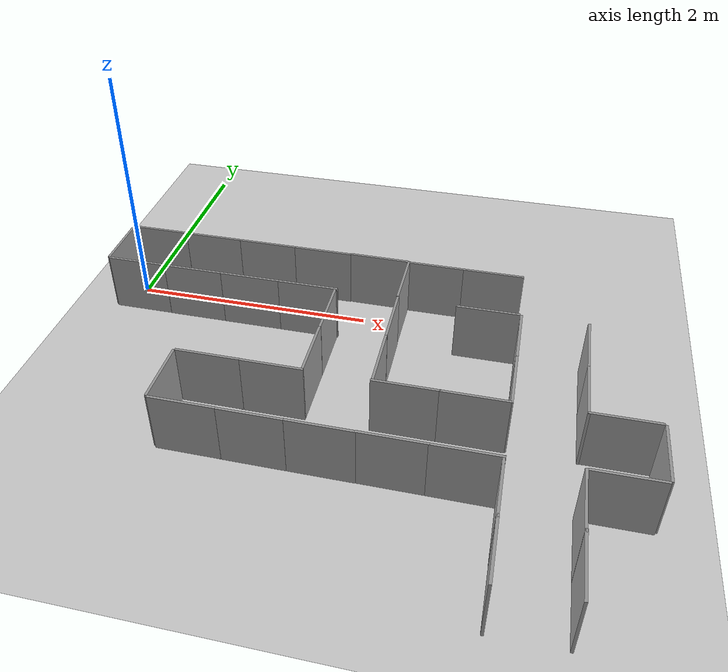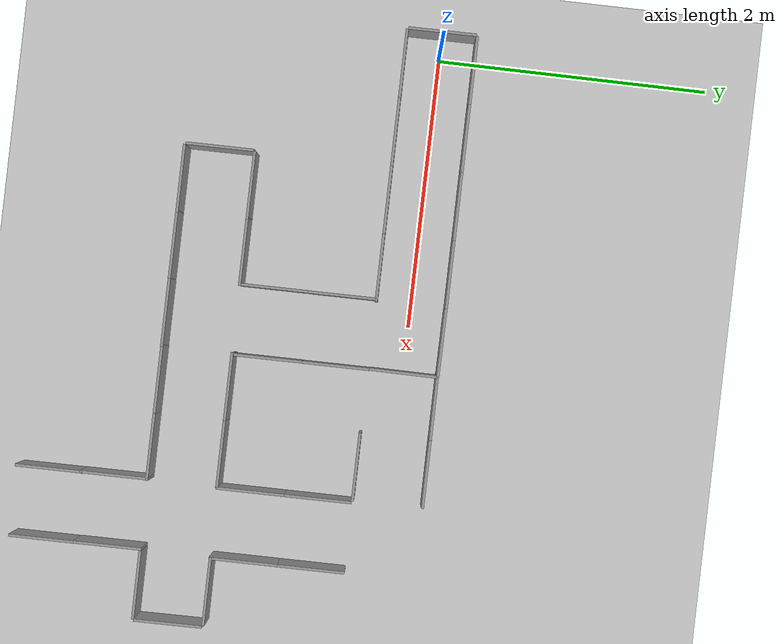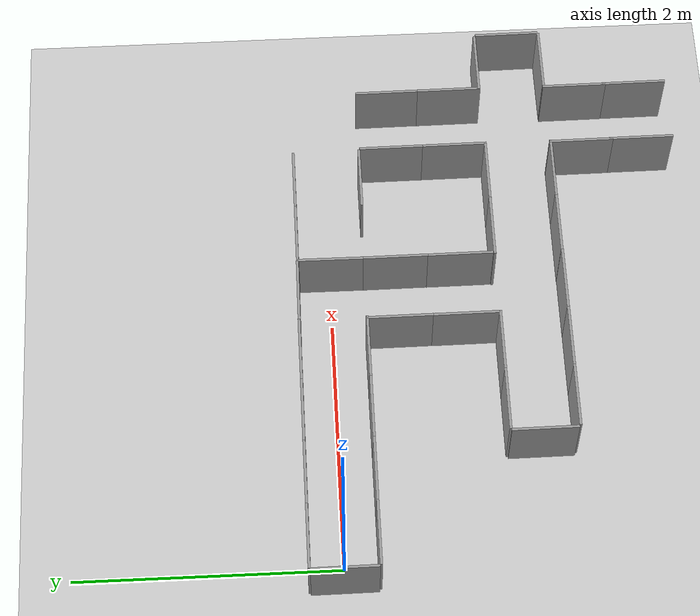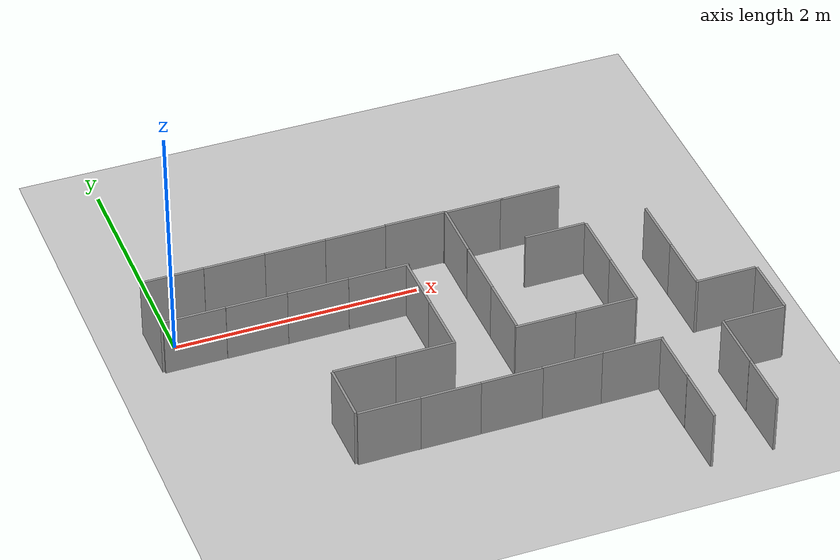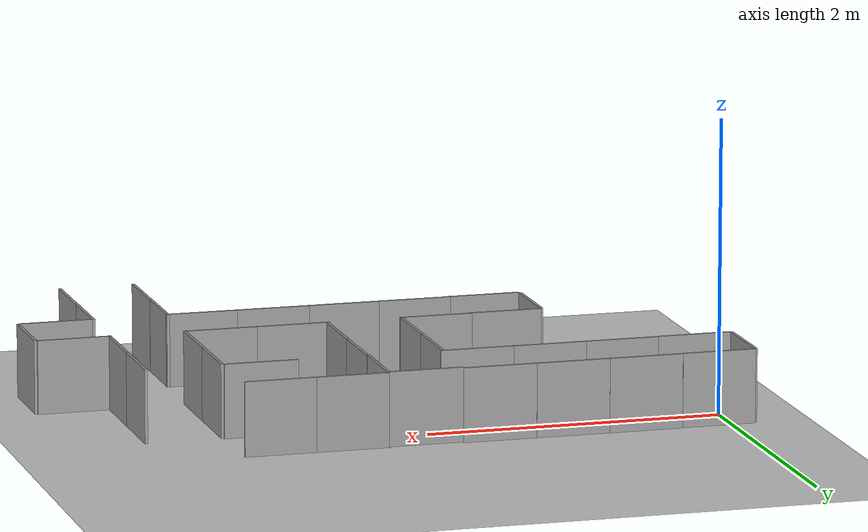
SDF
<sdf version="1.7">
 <world name="default">
  <model name="ground_plane">
   <static>1</static>
   <link name="link">
    <collision name="collision">
     <geometry><plane><normal>0 0 1</normal><size>100 100</size></plane></geometry>
     <surface><friction><ode><mu>100</mu><mu2>50</mu2></ode></friction></surface>
    </collision>
    <visual name="visual">
     <cast_shadows>0</cast_shadows>
     <geometry><plane><normal>0 0 1</normal><size>100 100</size></plane></geometry>
     <material>
      <script><uri>file://media/materials/scripts/gazebo.material</uri><name>Gazebo/Grey</name></script>
     </material>
    </visual>
   </link>
  </model>
  <light name="sun" type="directional">
   <pose>0 0 10 0 -0 0</pose>
   <diffuse>0.8 0.8 0.8 1</diffuse>
   <specular>0.2 0.2 0.2 1</specular>
   <attenuation>
    <range>1000</range>
    <constant>0.9</constant>
    <linear>0.01</linear>
    <quadratic>0.001</quadratic>
   </attenuation>
   <direction>-0.5 0.1 -0.9</direction>
   <spot><inner_angle>0</inner_angle><outer_angle>0</outer_angle><falloff>0</falloff></spot>
  </light>
  <scene><shadows>0</shadows><ambient>0.4 0.4 0.4 1</ambient><background>0.7 0.7 0.7 1</background></scene>
  <physics type="ode">
   <real_time_update_rate>1000</real_time_update_rate>
   <max_step_size>0.001</max_step_size>
   <real_time_factor>1</real_time_factor>
   <ode>
    <solver>
     <type>quick</type>
     <iters>150</iters>
     <precon_iters>0</precon_iters>
     <sor>1.4</sor>
     <use_dynamic_moi_rescaling>1</use_dynamic_moi_rescaling>
    </solver>
    <constraints>
     <cfm>1e-05</cfm>
     <erp>0.2</erp>
     <contact_max_correcting_vel>2000</contact_max_correcting_vel>
     <contact_surface_layer>0.01</contact_surface_layer>
    </constraints>
   </ode>
  </physics>
  <gravity>0 0 -9.8</gravity>
  <magnetic_field>6e-06 2.3e-05 -4.2e-05</magnetic_field>
  <atmosphere type="adiabatic"/>
  <spherical_coordinates>
   <surface_model>EARTH_WGS84</surface_model>
   <latitude_deg>0</latitude_deg>
   <longitude_deg>0</longitude_deg>
   <elevation>0</elevation>
   <heading_deg>0</heading_deg>
  </spherical_coordinates>
  <model name="hsl_module_1">
   <link name="link_2_clone">
    <inertial>
     <mass>1</mass>
     <inertia><ixx>0.01</ixx><ixy>0</ixy><ixz>0</ixz><iyy>0.02</iyy><iyz>0</iyz><izz>0.01</izz></inertia>
    </inertial>
    <pose>0.088798 -0.257146 0 0 -0 0</pose>
    <visual name="visual">
     <geometry><box><size>0.5 0.02 0.5</size></box></geometry>
     <material>
      <lighting>1</lighting>
      <script><uri>file://media/materials/scripts/gazebo.material</uri><name>Gazebo/Grey</name></script>
      <shader type="pixel"><normal_map>__default__</normal_map></shader>
      <ambient>0.3 0.3 0.3 1</ambient>
      <diffuse>0.7 0.7 0.7 1</diffuse>
      <specular>0.01 0.01 0.01 1</specular>
      <emissive>0 0 0 1</emissive>
     </material>
    </visual>
    <collision name="collision">
     <geometry><box><size>0.5 0.02 0.5</size></box></geometry>
     <surface>
      <friction>
       <ode><mu>1</mu><mu2>1</mu2><fdir1>0 0 0</fdir1><slip1>0</slip1><slip2>0</slip2></ode>
       <torsional>
        <coefficient>1</coefficient>
        <patch_radius>0</patch_radius>
        <surface_radius>0</surface_radius>
        <use_patch_radius>1</use_patch_radius>
        <ode><slip>0</slip></ode>
       </torsional>
      </friction>
      <bounce><restitution_coefficient>0</restitution_coefficient><threshold>1e+06</threshold></bounce>
      <contact>
       <collide_without_contact>0</collide_without_contact>
       <collide_without_contact_bitmask>1</collide_without_contact_bitmask>
       <collide_bitmask>1</collide_bitmask>
       <ode>
        <soft_cfm>0</soft_cfm>
        <soft_erp>0.2</soft_erp>
        <kp>1e+13</kp>
        <kd>1</kd>
        <max_vel>0.01</max_vel>
        <min_depth>0</min_depth>
       </ode>
       <bullet>
        <split_impulse>1</split_impulse>
        <split_impulse_penetration_threshold>-0.01</split_impulse_penetration_threshold>
        <soft_cfm>0</soft_cfm>
        <soft_erp>0.2</soft_erp>
        <kp>1e+13</kp>
        <kd>1</kd>
       </bullet>
      </contact>
     </surface>
    </collision>
   </link>
   <link name="link_2_clone_clone">
    <inertial>
     <mass>1</mass>
     <inertia><ixx>0.01</ixx><ixy>0</ixy><ixz>0</ixz><iyy>0.02</iyy><iyz>0</iyz><izz>0.01</izz></inertia>
    </inertial>
    <pose>-0.171704 0.000465 0 0 -0 1.57697</pose>
    <visual name="visual">
     <geometry><box><size>0.5 0.02 0.5</size></box></geometry>
     <material>
      <lighting>1</lighting>
      <script><uri>file://media/materials/scripts/gazebo.material</uri><name>Gazebo/Grey</name></script>
      <shader type="pixel"><normal_map>__default__</normal_map></shader>
      <ambient>0.3 0.3 0.3 1</ambient>
      <diffuse>0.7 0.7 0.7 1</diffuse>
      <specular>0.01 0.01 0.01 1</specular>
      <emissive>0 0 0 1</emissive>
     </material>
    </visual>
    <collision name="collision">
     <geometry><box><size>0.5 0.02 0.5</size></box></geometry>
     <surface>
      <friction>
       <ode><mu>1</mu><mu2>1</mu2><fdir1>0 0 0</fdir1><slip1>0</slip1><slip2>0</slip2></ode>
       <torsional>
        <coefficient>1</coefficient>
        <patch_radius>0</patch_radius>
        <surface_radius>0</surface_radius>
        <use_patch_radius>1</use_patch_radius>
        <ode><slip>0</slip></ode>
       </torsional>
      </friction>
      <bounce><restitution_coefficient>0</restitution_coefficient><threshold>1e+06</threshold></bounce>
      <contact>
       <collide_without_contact>0</collide_without_contact>
       <collide_without_contact_bitmask>1</collide_without_contact_bitmask>
       <collide_bitmask>1</collide_bitmask>
       <ode>
        <soft_cfm>0</soft_cfm>
        <soft_erp>0.2</soft_erp>
        <kp>1e+13</kp>
        <kd>1</kd>
        <max_vel>0.01</max_vel>
        <min_depth>0</min_depth>
       </ode>
       <bullet>
        <split_impulse>1</split_impulse>
        <split_impulse_penetration_threshold>-0.01</split_impulse_penetration_threshold>
        <soft_cfm>0</soft_cfm>
        <soft_erp>0.2</soft_erp>
        <kp>1e+13</kp>
        <kd>1</kd>
       </bullet>
      </contact>
     </surface>
    </collision>
   </link>
   <link name="link_2_clone_clone_0">
    <inertial>
     <mass>1</mass>
     <inertia><ixx>0.01</ixx><ixy>0</ixy><ixz>0</ixz><iyy>0.02</iyy><iyz>0</iyz><izz>0.01</izz></inertia>
    </inertial>
    <pose>0.082906 0.256681 0 0 -0 0</pose>
    <visual name="visual">
     <geometry><box><size>0.5 0.02 0.5</size></box></geometry>
     <material>
      <lighting>1</lighting>
      <script><uri>file://media/materials/scripts/gazebo.material</uri><name>Gazebo/Grey</name></script>
      <shader type="pixel"><normal_map>__default__</normal_map></shader>
      <ambient>0.3 0.3 0.3 1</ambient>
      <diffuse>0.7 0.7 0.7 1</diffuse>
      <specular>0.01 0.01 0.01 1</specular>
      <emissive>0 0 0 1</emissive>
     </material>
    </visual>
    <collision name="collision">
     <geometry><box><size>0.5 0.02 0.5</size></box></geometry>
     <surface>
      <friction>
       <ode><mu>1</mu><mu2>1</mu2><fdir1>0 0 0</fdir1><slip1>0</slip1><slip2>0</slip2></ode>
       <torsional>
        <coefficient>1</coefficient>
        <patch_radius>0</patch_radius>
        <surface_radius>0</surface_radius>
        <use_patch_radius>1</use_patch_radius>
        <ode><slip>0</slip></ode>
       </torsional>
      </friction>
      <bounce><restitution_coefficient>0</restitution_coefficient><threshold>1e+06</threshold></bounce>
      <contact>
       <collide_without_contact>0</collide_without_contact>
       <collide_without_contact_bitmask>1</collide_without_contact_bitmask>
       <collide_bitmask>1</collide_bitmask>
       <ode>
        <soft_cfm>0</soft_cfm>
        <soft_erp>0.2</soft_erp>
        <kp>1e+13</kp>
        <kd>1</kd>
        <max_vel>0.01</max_vel>
        <min_depth>0</min_depth>
       </ode>
       <bullet>
        <split_impulse>1</split_impulse>
        <split_impulse_penetration_threshold>-0.01</split_impulse_penetration_threshold>
        <soft_cfm>0</soft_cfm>
        <soft_erp>0.2</soft_erp>
        <kp>1e+13</kp>
        <kd>1</kd>
       </bullet>
      </contact>
     </surface>
    </collision>
   </link>
   <static>0</static>
   <pose>0.002202 0.000766 0.251418 0 -0 0</pose>
  </model>
  <model name="hsl_module_2">
   <link name="link_2_clone">
    <inertial>
     <mass>1</mass>
     <inertia><ixx>0.01</ixx><ixy>0</ixy><ixz>0</ixz><iyy>0.02</iyy><iyz>0</iyz><izz>0.01</izz></inertia>
    </inertial>
    <pose>-0.318213 -0.417987 0.25 0 -0 0</pose>
    <visual name="visual">
     <geometry><box><size>0.5 0.02 0.5</size></box></geometry>
     <material>
      <lighting>1</lighting>
      <script><uri>file://media/materials/scripts/gazebo.material</uri><name>Gazebo/Grey</name></script>
      <shader type="pixel"><normal_map>__default__</normal_map></shader>
      <ambient>0.3 0.3 0.3 1</ambient>
      <diffuse>0.7 0.7 0.7 1</diffuse>
      <specular>0.01 0.01 0.01 1</specular>
      <emissive>0 0 0 1</emissive>
     </material>
    </visual>
    <collision name="collision">
     <geometry><box><size>0.5 0.02 0.5</size></box></geometry>
     <surface>
      <friction>
       <ode><mu>1</mu><mu2>1</mu2><fdir1>0 0 0</fdir1><slip1>0</slip1><slip2>0</slip2></ode>
       <torsional>
        <coefficient>1</coefficient>
        <patch_radius>0</patch_radius>
        <surface_radius>0</surface_radius>
        <use_patch_radius>1</use_patch_radius>
        <ode><slip>0</slip></ode>
       </torsional>
      </friction>
      <bounce><restitution_coefficient>0</restitution_coefficient><threshold>1e+06</threshold></bounce>
      <contact>
       <collide_without_contact>0</collide_without_contact>
       <collide_without_contact_bitmask>1</collide_without_contact_bitmask>
       <collide_bitmask>1</collide_bitmask>
       <ode>
        <soft_cfm>0</soft_cfm>
        <soft_erp>0.2</soft_erp>
        <kp>1e+13</kp>
        <kd>1</kd>
        <max_vel>0.01</max_vel>
        <min_depth>0</min_depth>
       </ode>
       <bullet>
        <split_impulse>1</split_impulse>
        <split_impulse_penetration_threshold>-0.01</split_impulse_penetration_threshold>
        <soft_cfm>0</soft_cfm>
        <soft_erp>0.2</soft_erp>
        <kp>1e+13</kp>
        <kd>1</kd>
       </bullet>
      </contact>
     </surface>
    </collision>
   </link>
   <link name="link_2_clone_clone_0">
    <inertial>
     <mass>1</mass>
     <inertia><ixx>0.01</ixx><ixy>0</ixy><ixz>0</ixz><iyy>0.02</iyy><iyz>0</iyz><izz>0.01</izz></inertia>
    </inertial>
    <pose>-0.324105 0.095839 0.25 0 -0 0</pose>
    <visual name="visual">
     <geometry><box><size>0.5 0.02 0.5</size></box></geometry>
     <material>
      <lighting>1</lighting>
      <script><uri>file://media/materials/scripts/gazebo.material</uri><name>Gazebo/Grey</name></script>
      <shader type="pixel"><normal_map>__default__</normal_map></shader>
      <ambient>0.3 0.3 0.3 1</ambient>
      <diffuse>0.7 0.7 0.7 1</diffuse>
      <specular>0.01 0.01 0.01 1</specular>
      <emissive>0 0 0 1</emissive>
     </material>
    </visual>
    <collision name="collision">
     <geometry><box><size>0.5 0.02 0.5</size></box></geometry>
     <surface>
      <friction>
       <ode><mu>1</mu><mu2>1</mu2><fdir1>0 0 0</fdir1><slip1>0</slip1><slip2>0</slip2></ode>
       <torsional>
        <coefficient>1</coefficient>
        <patch_radius>0</patch_radius>
        <surface_radius>0</surface_radius>
        <use_patch_radius>1</use_patch_radius>
        <ode><slip>0</slip></ode>
       </torsional>
      </friction>
      <bounce><restitution_coefficient>0</restitution_coefficient><threshold>1e+06</threshold></bounce>
      <contact>
       <collide_without_contact>0</collide_without_contact>
       <collide_without_contact_bitmask>1</collide_without_contact_bitmask>
       <collide_bitmask>1</collide_bitmask>
       <ode>
        <soft_cfm>0</soft_cfm>
        <soft_erp>0.2</soft_erp>
        <kp>1e+13</kp>
        <kd>1</kd>
        <max_vel>0.01</max_vel>
        <min_depth>0</min_depth>
       </ode>
       <bullet>
        <split_impulse>1</split_impulse>
        <split_impulse_penetration_threshold>-0.01</split_impulse_penetration_threshold>
        <soft_cfm>0</soft_cfm>
        <soft_erp>0.2</soft_erp>
        <kp>1e+13</kp>
        <kd>1</kd>
       </bullet>
      </contact>
     </surface>
    </collision>
   </link>
   <static>0</static>
   <pose>0.909912 0.161139 0 0 -0 0</pose>
  </model>
  <model name="hsl_module_2_clone">
   <link name="link_2_clone">
    <inertial>
     <mass>1</mass>
     <inertia><ixx>0.01</ixx><ixy>0</ixy><ixz>0</ixz><iyy>0.02</iyy><iyz>0</iyz><izz>0.01</izz></inertia>
    </inertial>
    <pose>-0.318213 -0.417987 0.25 0 -0 0</pose>
    <visual name="visual">
     <geometry><box><size>0.5 0.02 0.5</size></box></geometry>
     <material>
      <lighting>1</lighting>
      <script><uri>file://media/materials/scripts/gazebo.material</uri><name>Gazebo/Grey</name></script>
      <shader type="pixel"><normal_map>__default__</normal_map></shader>
      <ambient>0.3 0.3 0.3 1</ambient>
      <diffuse>0.7 0.7 0.7 1</diffuse>
      <specular>0.01 0.01 0.01 1</specular>
      <emissive>0 0 0 1</emissive>
     </material>
    </visual>
    <collision name="collision">
     <geometry><box><size>0.5 0.02 0.5</size></box></geometry>
     <surface>
      <friction>
       <ode><mu>1</mu><mu2>1</mu2><fdir1>0 0 0</fdir1><slip1>0</slip1><slip2>0</slip2></ode>
       <torsional>
        <coefficient>1</coefficient>
        <patch_radius>0</patch_radius>
        <surface_radius>0</surface_radius>
        <use_patch_radius>1</use_patch_radius>
        <ode><slip>0</slip></ode>
       </torsional>
      </friction>
      <bounce><restitution_coefficient>0</restitution_coefficient><threshold>1e+06</threshold></bounce>
      <contact>
       <collide_without_contact>0</collide_without_contact>
       <collide_without_contact_bitmask>1</collide_without_contact_bitmask>
       <collide_bitmask>1</collide_bitmask>
       <ode>
        <soft_cfm>0</soft_cfm>
        <soft_erp>0.2</soft_erp>
        <kp>1e+13</kp>
        <kd>1</kd>
        <max_vel>0.01</max_vel>
        <min_depth>0</min_depth>
       </ode>
       <bullet>
        <split_impulse>1</split_impulse>
        <split_impulse_penetration_threshold>-0.01</split_impulse_penetration_threshold>
        <soft_cfm>0</soft_cfm>
        <soft_erp>0.2</soft_erp>
        <kp>1e+13</kp>
        <kd>1</kd>
       </bullet>
      </contact>
     </surface>
    </collision>
   </link>
   <link name="link_2_clone_clone_0">
    <inertial>
     <mass>1</mass>
     <inertia><ixx>0.01</ixx><ixy>0</ixy><ixz>0</ixz><iyy>0.02</iyy><iyz>0</iyz><izz>0.01</izz></inertia>
    </inertial>
    <pose>-0.324105 0.095839 0.25 0 -0 0</pose>
    <visual name="visual">
     <geometry><box><size>0.5 0.02 0.5</size></box></geometry>
     <material>
      <lighting>1</lighting>
      <script><uri>file://media/materials/scripts/gazebo.material</uri><name>Gazebo/Grey</name></script>
      <shader type="pixel"><normal_map>__default__</normal_map></shader>
      <ambient>0.3 0.3 0.3 1</ambient>
      <diffuse>0.7 0.7 0.7 1</diffuse>
      <specular>0.01 0.01 0.01 1</specular>
      <emissive>0 0 0 1</emissive>
     </material>
    </visual>
    <collision name="collision">
     <geometry><box><size>0.5 0.02 0.5</size></box></geometry>
     <surface>
      <friction>
       <ode><mu>1</mu><mu2>1</mu2><fdir1>0 0 0</fdir1><slip1>0</slip1><slip2>0</slip2></ode>
       <torsional>
        <coefficient>1</coefficient>
        <patch_radius>0</patch_radius>
        <surface_radius>0</surface_radius>
        <use_patch_radius>1</use_patch_radius>
        <ode><slip>0</slip></ode>
       </torsional>
      </friction>
      <bounce><restitution_coefficient>0</restitution_coefficient><threshold>1e+06</threshold></bounce>
      <contact>
       <collide_without_contact>0</collide_without_contact>
       <collide_without_contact_bitmask>1</collide_without_contact_bitmask>
       <collide_bitmask>1</collide_bitmask>
       <ode>
        <soft_cfm>0</soft_cfm>
        <soft_erp>0.2</soft_erp>
        <kp>1e+13</kp>
        <kd>1</kd>
        <max_vel>0.01</max_vel>
        <min_depth>0</min_depth>
       </ode>
       <bullet>
        <split_impulse>1</split_impulse>
        <split_impulse_penetration_threshold>-0.01</split_impulse_penetration_threshold>
        <soft_cfm>0</soft_cfm>
        <soft_erp>0.2</soft_erp>
        <kp>1e+13</kp>
        <kd>1</kd>
       </bullet>
      </contact>
     </surface>
    </collision>
   </link>
   <static>0</static>
   <pose>1.40798 0.16075 0 0 -0 0</pose>
  </model>
  <model name="hsl_module_2_clone_clone">
   <link name="link_2_clone">
    <inertial>
     <mass>1</mass>
     <inertia><ixx>0.01</ixx><ixy>0</ixy><ixz>0</ixz><iyy>0.02</iyy><iyz>0</iyz><izz>0.01</izz></inertia>
    </inertial>
    <pose>-0.318213 -0.417987 0.25 0 -0 0</pose>
    <visual name="visual">
     <geometry><box><size>0.5 0.02 0.5</size></box></geometry>
     <material>
      <lighting>1</lighting>
      <script><uri>file://media/materials/scripts/gazebo.material</uri><name>Gazebo/Grey</name></script>
      <shader type="pixel"><normal_map>__default__</normal_map></shader>
      <ambient>0.3 0.3 0.3 1</ambient>
      <diffuse>0.7 0.7 0.7 1</diffuse>
      <specular>0.01 0.01 0.01 1</specular>
      <emissive>0 0 0 1</emissive>
     </material>
    </visual>
    <collision name="collision">
     <geometry><box><size>0.5 0.02 0.5</size></box></geometry>
     <surface>
      <friction>
       <ode><mu>1</mu><mu2>1</mu2><fdir1>0 0 0</fdir1><slip1>0</slip1><slip2>0</slip2></ode>
       <torsional>
        <coefficient>1</coefficient>
        <patch_radius>0</patch_radius>
        <surface_radius>0</surface_radius>
        <use_patch_radius>1</use_patch_radius>
        <ode><slip>0</slip></ode>
       </torsional>
      </friction>
      <bounce><restitution_coefficient>0</restitution_coefficient><threshold>1e+06</threshold></bounce>
      <contact>
       <collide_without_contact>0</collide_without_contact>
       <collide_without_contact_bitmask>1</collide_without_contact_bitmask>
       <collide_bitmask>1</collide_bitmask>
       <ode>
        <soft_cfm>0</soft_cfm>
        <soft_erp>0.2</soft_erp>
        <kp>1e+13</kp>
        <kd>1</kd>
        <max_vel>0.01</max_vel>
        <min_depth>0</min_depth>
       </ode>
       <bullet>
        <split_impulse>1</split_impulse>
        <split_impulse_penetration_threshold>-0.01</split_impulse_penetration_threshold>
        <soft_cfm>0</soft_cfm>
        <soft_erp>0.2</soft_erp>
        <kp>1e+13</kp>
        <kd>1</kd>
       </bullet>
      </contact>
     </surface>
    </collision>
   </link>
   <link name="link_2_clone_clone_0">
    <inertial>
     <mass>1</mass>
     <inertia><ixx>0.01</ixx><ixy>0</ixy><ixz>0</ixz><iyy>0.02</iyy><iyz>0</iyz><izz>0.01</izz></inertia>
    </inertial>
    <pose>-0.324105 0.095839 0.25 0 -0 0</pose>
    <visual name="visual">
     <geometry><box><size>0.5 0.02 0.5</size></box></geometry>
     <material>
      <lighting>1</lighting>
      <script><uri>file://media/materials/scripts/gazebo.material</uri><name>Gazebo/Grey</name></script>
      <shader type="pixel"><normal_map>__default__</normal_map></shader>
      <ambient>0.3 0.3 0.3 1</ambient>
      <diffuse>0.7 0.7 0.7 1</diffuse>
      <specular>0.01 0.01 0.01 1</specular>
      <emissive>0 0 0 1</emissive>
     </material>
    </visual>
    <collision name="collision">
     <geometry><box><size>0.5 0.02 0.5</size></box></geometry>
     <surface>
      <friction>
       <ode><mu>1</mu><mu2>1</mu2><fdir1>0 0 0</fdir1><slip1>0</slip1><slip2>0</slip2></ode>
       <torsional>
        <coefficient>1</coefficient>
        <patch_radius>0</patch_radius>
        <surface_radius>0</surface_radius>
        <use_patch_radius>1</use_patch_radius>
        <ode><slip>0</slip></ode>
       </torsional>
      </friction>
      <bounce><restitution_coefficient>0</restitution_coefficient><threshold>1e+06</threshold></bounce>
      <contact>
       <collide_without_contact>0</collide_without_contact>
       <collide_without_contact_bitmask>1</collide_without_contact_bitmask>
       <collide_bitmask>1</collide_bitmask>
       <ode>
        <soft_cfm>0</soft_cfm>
        <soft_erp>0.2</soft_erp>
        <kp>1e+13</kp>
        <kd>1</kd>
        <max_vel>0.01</max_vel>
        <min_depth>0</min_depth>
       </ode>
       <bullet>
        <split_impulse>1</split_impulse>
        <split_impulse_penetration_threshold>-0.01</split_impulse_penetration_threshold>
        <soft_cfm>0</soft_cfm>
        <soft_erp>0.2</soft_erp>
        <kp>1e+13</kp>
        <kd>1</kd>
       </bullet>
      </contact>
     </surface>
    </collision>
   </link>
   <static>0</static>
   <pose>1.9059 0.160163 0 0 -0 0</pose>
  </model>
  <model name="hsl_module_3">
   <link name="link_2_clone">
    <inertial>
     <mass>1</mass>
     <inertia><ixx>0.01</ixx><ixy>0</ixy><ixz>0</ixz><iyy>0.02</iyy><iyz>0</iyz><izz>0.01</izz></inertia>
    </inertial>
    <pose>0.212503 -0.126383 0 0 -0 0</pose>
    <visual name="visual">
     <geometry><box><size>0.5 0.02 0.5</size></box></geometry>
     <material>
      <lighting>1</lighting>
      <script><uri>file://media/materials/scripts/gazebo.material</uri><name>Gazebo/Grey</name></script>
      <shader type="pixel"><normal_map>__default__</normal_map></shader>
      <ambient>0.3 0.3 0.3 1</ambient>
      <diffuse>0.7 0.7 0.7 1</diffuse>
      <specular>0.01 0.01 0.01 1</specular>
      <emissive>0 0 0 1</emissive>
     </material>
    </visual>
    <collision name="collision">
     <geometry><box><size>0.5 0.02 0.5</size></box></geometry>
     <surface>
      <friction>
       <ode><mu>1</mu><mu2>1</mu2><fdir1>0 0 0</fdir1><slip1>0</slip1><slip2>0</slip2></ode>
       <torsional>
        <coefficient>1</coefficient>
        <patch_radius>0</patch_radius>
        <surface_radius>0</surface_radius>
        <use_patch_radius>1</use_patch_radius>
        <ode><slip>0</slip></ode>
       </torsional>
      </friction>
      <bounce><restitution_coefficient>0</restitution_coefficient><threshold>1e+06</threshold></bounce>
      <contact>
       <collide_without_contact>0</collide_without_contact>
       <collide_without_contact_bitmask>1</collide_without_contact_bitmask>
       <collide_bitmask>1</collide_bitmask>
       <ode>
        <soft_cfm>0</soft_cfm>
        <soft_erp>0.2</soft_erp>
        <kp>1e+13</kp>
        <kd>1</kd>
        <max_vel>0.01</max_vel>
        <min_depth>0</min_depth>
       </ode>
       <bullet>
        <split_impulse>1</split_impulse>
        <split_impulse_penetration_threshold>-0.01</split_impulse_penetration_threshold>
        <soft_cfm>0</soft_cfm>
        <soft_erp>0.2</soft_erp>
        <kp>1e+13</kp>
        <kd>1</kd>
       </bullet>
      </contact>
     </surface>
    </collision>
   </link>
   <link name="link_2_clone_clone">
    <inertial>
     <mass>1</mass>
     <inertia><ixx>0.01</ixx><ixy>0</ixy><ixz>0</ixz><iyy>0.02</iyy><iyz>0</iyz><izz>0.01</izz></inertia>
    </inertial>
    <pose>-0.040799 0.125917 0 0 -0 1.57298</pose>
    <visual name="visual">
     <geometry><box><size>0.5 0.02 0.5</size></box></geometry>
     <material>
      <lighting>1</lighting>
      <script><uri>file://media/materials/scripts/gazebo.material</uri><name>Gazebo/Grey</name></script>
      <shader type="pixel"><normal_map>__default__</normal_map></shader>
      <ambient>0.3 0.3 0.3 1</ambient>
      <diffuse>0.7 0.7 0.7 1</diffuse>
      <specular>0.01 0.01 0.01 1</specular>
      <emissive>0 0 0 1</emissive>
     </material>
    </visual>
    <collision name="collision">
     <geometry><box><size>0.5 0.02 0.5</size></box></geometry>
     <surface>
      <friction>
       <ode><mu>1</mu><mu2>1</mu2><fdir1>0 0 0</fdir1><slip1>0</slip1><slip2>0</slip2></ode>
       <torsional>
        <coefficient>1</coefficient>
        <patch_radius>0</patch_radius>
        <surface_radius>0</surface_radius>
        <use_patch_radius>1</use_patch_radius>
        <ode><slip>0</slip></ode>
       </torsional>
      </friction>
      <bounce><restitution_coefficient>0</restitution_coefficient><threshold>1e+06</threshold></bounce>
      <contact>
       <collide_without_contact>0</collide_without_contact>
       <collide_without_contact_bitmask>1</collide_without_contact_bitmask>
       <collide_bitmask>1</collide_bitmask>
       <ode>
        <soft_cfm>0</soft_cfm>
        <soft_erp>0.2</soft_erp>
        <kp>1e+13</kp>
        <kd>1</kd>
        <max_vel>0.01</max_vel>
        <min_depth>0</min_depth>
       </ode>
       <bullet>
        <split_impulse>1</split_impulse>
        <split_impulse_penetration_threshold>-0.01</split_impulse_penetration_threshold>
        <soft_cfm>0</soft_cfm>
        <soft_erp>0.2</soft_erp>
        <kp>1e+13</kp>
        <kd>1</kd>
       </bullet>
      </contact>
     </surface>
    </collision>
   </link>
   <static>0</static>
   <pose>2.29336 0.124927 0.255067 0 -0 3.13436</pose>
  </model>
  <model name="hsl_module_2_0">
   <link name="link_2_clone">
    <inertial>
     <mass>1</mass>
     <inertia><ixx>0.01</ixx><ixy>0</ixy><ixz>0</ixz><iyy>0.02</iyy><iyz>0</iyz><izz>0.01</izz></inertia>
    </inertial>
    <pose>-0.318213 -0.417987 0.25 0 -0 0</pose>
    <visual name="visual">
     <geometry><box><size>0.5 0.02 0.5</size></box></geometry>
     <material>
      <lighting>1</lighting>
      <script><uri>file://media/materials/scripts/gazebo.material</uri><name>Gazebo/Grey</name></script>
      <shader type="pixel"><normal_map>__default__</normal_map></shader>
      <ambient>0.3 0.3 0.3 1</ambient>
      <diffuse>0.7 0.7 0.7 1</diffuse>
      <specular>0.01 0.01 0.01 1</specular>
      <emissive>0 0 0 1</emissive>
     </material>
    </visual>
    <collision name="collision">
     <geometry><box><size>0.5 0.02 0.5</size></box></geometry>
     <surface>
      <friction>
       <ode><mu>1</mu><mu2>1</mu2><fdir1>0 0 0</fdir1><slip1>0</slip1><slip2>0</slip2></ode>
       <torsional>
        <coefficient>1</coefficient>
        <patch_radius>0</patch_radius>
        <surface_radius>0</surface_radius>
        <use_patch_radius>1</use_patch_radius>
        <ode><slip>0</slip></ode>
       </torsional>
      </friction>
      <bounce><restitution_coefficient>0</restitution_coefficient><threshold>1e+06</threshold></bounce>
      <contact>
       <collide_without_contact>0</collide_without_contact>
       <collide_without_contact_bitmask>1</collide_without_contact_bitmask>
       <collide_bitmask>1</collide_bitmask>
       <ode>
        <soft_cfm>0</soft_cfm>
        <soft_erp>0.2</soft_erp>
        <kp>1e+13</kp>
        <kd>1</kd>
        <max_vel>0.01</max_vel>
        <min_depth>0</min_depth>
       </ode>
       <bullet>
        <split_impulse>1</split_impulse>
        <split_impulse_penetration_threshold>-0.01</split_impulse_penetration_threshold>
        <soft_cfm>0</soft_cfm>
        <soft_erp>0.2</soft_erp>
        <kp>1e+13</kp>
        <kd>1</kd>
       </bullet>
      </contact>
     </surface>
    </collision>
   </link>
   <link name="link_2_clone_clone_0">
    <inertial>
     <mass>1</mass>
     <inertia><ixx>0.01</ixx><ixy>0</ixy><ixz>0</ixz><iyy>0.02</iyy><iyz>0</iyz><izz>0.01</izz></inertia>
    </inertial>
    <pose>-0.324105 0.095839 0.25 0 -0 0</pose>
    <visual name="visual">
     <geometry><box><size>0.5 0.02 0.5</size></box></geometry>
     <material>
      <lighting>1</lighting>
      <script><uri>file://media/materials/scripts/gazebo.material</uri><name>Gazebo/Grey</name></script>
      <shader type="pixel"><normal_map>__default__</normal_map></shader>
      <ambient>0.3 0.3 0.3 1</ambient>
      <diffuse>0.7 0.7 0.7 1</diffuse>
      <specular>0.01 0.01 0.01 1</specular>
      <emissive>0 0 0 1</emissive>
     </material>
    </visual>
    <collision name="collision">
     <geometry><box><size>0.5 0.02 0.5</size></box></geometry>
     <surface>
      <friction>
       <ode><mu>1</mu><mu2>1</mu2><fdir1>0 0 0</fdir1><slip1>0</slip1><slip2>0</slip2></ode>
       <torsional>
        <coefficient>1</coefficient>
        <patch_radius>0</patch_radius>
        <surface_radius>0</surface_radius>
        <use_patch_radius>1</use_patch_radius>
        <ode><slip>0</slip></ode>
       </torsional>
      </friction>
      <bounce><restitution_coefficient>0</restitution_coefficient><threshold>1e+06</threshold></bounce>
      <contact>
       <collide_without_contact>0</collide_without_contact>
       <collide_without_contact_bitmask>1</collide_without_contact_bitmask>
       <collide_bitmask>1</collide_bitmask>
       <ode>
        <soft_cfm>0</soft_cfm>
        <soft_erp>0.2</soft_erp>
        <kp>1e+13</kp>
        <kd>1</kd>
        <max_vel>0.01</max_vel>
        <min_depth>0</min_depth>
       </ode>
       <bullet>
        <split_impulse>1</split_impulse>
        <split_impulse_penetration_threshold>-0.01</split_impulse_penetration_threshold>
        <soft_cfm>0</soft_cfm>
        <soft_erp>0.2</soft_erp>
        <kp>1e+13</kp>
        <kd>1</kd>
       </bullet>
      </contact>
     </surface>
    </collision>
   </link>
   <static>0</static>
   <pose>2.24183 -0.822097 0 0 0 -1.56536</pose>
  </model>
  <model name="hsl_module_2_0_clone">
   <link name="link_2_clone">
    <inertial>
     <mass>1</mass>
     <inertia><ixx>0.01</ixx><ixy>0</ixy><ixz>0</ixz><iyy>0.02</iyy><iyz>0</iyz><izz>0.01</izz></inertia>
    </inertial>
    <pose>-0.318213 -0.417987 0.25 0 -0 0</pose>
    <visual name="visual">
     <geometry><box><size>0.5 0.02 0.5</size></box></geometry>
     <material>
      <lighting>1</lighting>
      <script><uri>file://media/materials/scripts/gazebo.material</uri><name>Gazebo/Grey</name></script>
      <shader type="pixel"><normal_map>__default__</normal_map></shader>
      <ambient>0.3 0.3 0.3 1</ambient>
      <diffuse>0.7 0.7 0.7 1</diffuse>
      <specular>0.01 0.01 0.01 1</specular>
      <emissive>0 0 0 1</emissive>
     </material>
    </visual>
    <collision name="collision">
     <geometry><box><size>0.5 0.02 0.5</size></box></geometry>
     <surface>
      <friction>
       <ode><mu>1</mu><mu2>1</mu2><fdir1>0 0 0</fdir1><slip1>0</slip1><slip2>0</slip2></ode>
       <torsional>
        <coefficient>1</coefficient>
        <patch_radius>0</patch_radius>
        <surface_radius>0</surface_radius>
        <use_patch_radius>1</use_patch_radius>
        <ode><slip>0</slip></ode>
       </torsional>
      </friction>
      <bounce><restitution_coefficient>0</restitution_coefficient><threshold>1e+06</threshold></bounce>
      <contact>
       <collide_without_contact>0</collide_without_contact>
       <collide_without_contact_bitmask>1</collide_without_contact_bitmask>
       <collide_bitmask>1</collide_bitmask>
       <ode>
        <soft_cfm>0</soft_cfm>
        <soft_erp>0.2</soft_erp>
        <kp>1e+13</kp>
        <kd>1</kd>
        <max_vel>0.01</max_vel>
        <min_depth>0</min_depth>
       </ode>
       <bullet>
        <split_impulse>1</split_impulse>
        <split_impulse_penetration_threshold>-0.01</split_impulse_penetration_threshold>
        <soft_cfm>0</soft_cfm>
        <soft_erp>0.2</soft_erp>
        <kp>1e+13</kp>
        <kd>1</kd>
       </bullet>
      </contact>
     </surface>
    </collision>
   </link>
   <link name="link_2_clone_clone_0">
    <inertial>
     <mass>1</mass>
     <inertia><ixx>0.01</ixx><ixy>0</ixy><ixz>0</ixz><iyy>0.02</iyy><iyz>0</iyz><izz>0.01</izz></inertia>
    </inertial>
    <pose>-0.324105 0.095839 0.25 0 -0 0</pose>
    <visual name="visual">
     <geometry><box><size>0.5 0.02 0.5</size></box></geometry>
     <material>
      <lighting>1</lighting>
      <script><uri>file://media/materials/scripts/gazebo.material</uri><name>Gazebo/Grey</name></script>
      <shader type="pixel"><normal_map>__default__</normal_map></shader>
      <ambient>0.3 0.3 0.3 1</ambient>
      <diffuse>0.7 0.7 0.7 1</diffuse>
      <specular>0.01 0.01 0.01 1</specular>
      <emissive>0 0 0 1</emissive>
     </material>
    </visual>
    <collision name="collision">
     <geometry><box><size>0.5 0.02 0.5</size></box></geometry>
     <surface>
      <friction>
       <ode><mu>1</mu><mu2>1</mu2><fdir1>0 0 0</fdir1><slip1>0</slip1><slip2>0</slip2></ode>
       <torsional>
        <coefficient>1</coefficient>
        <patch_radius>0</patch_radius>
        <surface_radius>0</surface_radius>
        <use_patch_radius>1</use_patch_radius>
        <ode><slip>0</slip></ode>
       </torsional>
      </friction>
      <bounce><restitution_coefficient>0</restitution_coefficient><threshold>1e+06</threshold></bounce>
      <contact>
       <collide_without_contact>0</collide_without_contact>
       <collide_without_contact_bitmask>1</collide_without_contact_bitmask>
       <collide_bitmask>1</collide_bitmask>
       <ode>
        <soft_cfm>0</soft_cfm>
        <soft_erp>0.2</soft_erp>
        <kp>1e+13</kp>
        <kd>1</kd>
        <max_vel>0.01</max_vel>
        <min_depth>0</min_depth>
       </ode>
       <bullet>
        <split_impulse>1</split_impulse>
        <split_impulse_penetration_threshold>-0.01</split_impulse_penetration_threshold>
        <soft_cfm>0</soft_cfm>
        <soft_erp>0.2</soft_erp>
        <kp>1e+13</kp>
        <kd>1</kd>
       </bullet>
      </contact>
     </surface>
    </collision>
   </link>
   <static>0</static>
   <pose>2.24354 -1.31921 0 0 0 -1.56536</pose>
  </model>
  <model name="hsl_module_2_clone_clone_clone">
   <link name="link_2_clone">
    <inertial>
     <mass>1</mass>
     <inertia><ixx>0.01</ixx><ixy>0</ixy><ixz>0</ixz><iyy>0.02</iyy><iyz>0</iyz><izz>0.01</izz></inertia>
    </inertial>
    <pose>-0.318213 -0.417987 0.25 0 -0 0</pose>
    <visual name="visual">
     <geometry><box><size>0.5 0.02 0.5</size></box></geometry>
     <material>
      <lighting>1</lighting>
      <script><uri>file://media/materials/scripts/gazebo.material</uri><name>Gazebo/Grey</name></script>
      <shader type="pixel"><normal_map>__default__</normal_map></shader>
      <ambient>0.3 0.3 0.3 1</ambient>
      <diffuse>0.7 0.7 0.7 1</diffuse>
      <specular>0.01 0.01 0.01 1</specular>
      <emissive>0 0 0 1</emissive>
     </material>
    </visual>
    <collision name="collision">
     <geometry><box><size>0.5 0.02 0.5</size></box></geometry>
     <surface>
      <friction>
       <ode><mu>1</mu><mu2>1</mu2><fdir1>0 0 0</fdir1><slip1>0</slip1><slip2>0</slip2></ode>
       <torsional>
        <coefficient>1</coefficient>
        <patch_radius>0</patch_radius>
        <surface_radius>0</surface_radius>
        <use_patch_radius>1</use_patch_radius>
        <ode><slip>0</slip></ode>
       </torsional>
      </friction>
      <bounce><restitution_coefficient>0</restitution_coefficient><threshold>1e+06</threshold></bounce>
      <contact>
       <collide_without_contact>0</collide_without_contact>
       <collide_without_contact_bitmask>1</collide_without_contact_bitmask>
       <collide_bitmask>1</collide_bitmask>
       <ode>
        <soft_cfm>0</soft_cfm>
        <soft_erp>0.2</soft_erp>
        <kp>1e+13</kp>
        <kd>1</kd>
        <max_vel>0.01</max_vel>
        <min_depth>0</min_depth>
       </ode>
       <bullet>
        <split_impulse>1</split_impulse>
        <split_impulse_penetration_threshold>-0.01</split_impulse_penetration_threshold>
        <soft_cfm>0</soft_cfm>
        <soft_erp>0.2</soft_erp>
        <kp>1e+13</kp>
        <kd>1</kd>
       </bullet>
      </contact>
     </surface>
    </collision>
   </link>
   <link name="link_2_clone_clone_0">
    <inertial>
     <mass>1</mass>
     <inertia><ixx>0.01</ixx><ixy>0</ixy><ixz>0</ixz><iyy>0.02</iyy><iyz>0</iyz><izz>0.01</izz></inertia>
    </inertial>
    <pose>-0.324105 0.095839 0.25 0 -0 0</pose>
    <visual name="visual">
     <geometry><box><size>0.5 0.02 0.5</size></box></geometry>
     <material>
      <lighting>1</lighting>
      <script><uri>file://media/materials/scripts/gazebo.material</uri><name>Gazebo/Grey</name></script>
      <shader type="pixel"><normal_map>__default__</normal_map></shader>
      <ambient>0.3 0.3 0.3 1</ambient>
      <diffuse>0.7 0.7 0.7 1</diffuse>
      <specular>0.01 0.01 0.01 1</specular>
      <emissive>0 0 0 1</emissive>
     </material>
    </visual>
    <collision name="collision">
     <geometry><box><size>0.5 0.02 0.5</size></box></geometry>
     <surface>
      <friction>
       <ode><mu>1</mu><mu2>1</mu2><fdir1>0 0 0</fdir1><slip1>0</slip1><slip2>0</slip2></ode>
       <torsional>
        <coefficient>1</coefficient>
        <patch_radius>0</patch_radius>
        <surface_radius>0</surface_radius>
        <use_patch_radius>1</use_patch_radius>
        <ode><slip>0</slip></ode>
       </torsional>
      </friction>
      <bounce><restitution_coefficient>0</restitution_coefficient><threshold>1e+06</threshold></bounce>
      <contact>
       <collide_without_contact>0</collide_without_contact>
       <collide_without_contact_bitmask>1</collide_without_contact_bitmask>
       <collide_bitmask>1</collide_bitmask>
       <ode>
        <soft_cfm>0</soft_cfm>
        <soft_erp>0.2</soft_erp>
        <kp>1e+13</kp>
        <kd>1</kd>
        <max_vel>0.01</max_vel>
        <min_depth>0</min_depth>
       </ode>
       <bullet>
        <split_impulse>1</split_impulse>
        <split_impulse_penetration_threshold>-0.01</split_impulse_penetration_threshold>
        <soft_cfm>0</soft_cfm>
        <soft_erp>0.2</soft_erp>
        <kp>1e+13</kp>
        <kd>1</kd>
       </bullet>
      </contact>
     </surface>
    </collision>
   </link>
   <static>0</static>
   <pose>1.90903 -1.35537 0 0 -0 0</pose>
  </model>
  <model name="hsl_module_5">
   <link name="link_2_clone_clone">
    <inertial>
     <mass>1</mass>
     <inertia><ixx>0.01</ixx><ixy>0</ixy><ixz>0</ixz><iyy>0.02</iyy><iyz>0</iyz><izz>0.01</izz></inertia>
    </inertial>
    <pose>-0.444864 -0.291837 0.25 0 -0 1.57298</pose>
    <visual name="visual">
     <geometry><box><size>0.5 0.02 0.5</size></box></geometry>
     <material>
      <lighting>1</lighting>
      <script><uri>file://media/materials/scripts/gazebo.material</uri><name>Gazebo/Grey</name></script>
      <shader type="pixel"><normal_map>__default__</normal_map></shader>
      <ambient>0.3 0.3 0.3 1</ambient>
      <diffuse>0.7 0.7 0.7 1</diffuse>
      <specular>0.01 0.01 0.01 1</specular>
      <emissive>0 0 0 1</emissive>
     </material>
    </visual>
    <collision name="collision">
     <geometry><box><size>0.5 0.02 0.5</size></box></geometry>
     <surface>
      <friction>
       <ode><mu>1</mu><mu2>1</mu2><fdir1>0 0 0</fdir1><slip1>0</slip1><slip2>0</slip2></ode>
       <torsional>
        <coefficient>1</coefficient>
        <patch_radius>0</patch_radius>
        <surface_radius>0</surface_radius>
        <use_patch_radius>1</use_patch_radius>
        <ode><slip>0</slip></ode>
       </torsional>
      </friction>
      <bounce><restitution_coefficient>0</restitution_coefficient><threshold>1e+06</threshold></bounce>
      <contact>
       <collide_without_contact>0</collide_without_contact>
       <collide_without_contact_bitmask>1</collide_without_contact_bitmask>
       <collide_bitmask>1</collide_bitmask>
       <ode>
        <soft_cfm>0</soft_cfm>
        <soft_erp>0.2</soft_erp>
        <kp>1e+13</kp>
        <kd>1</kd>
        <max_vel>0.01</max_vel>
        <min_depth>0</min_depth>
       </ode>
       <bullet>
        <split_impulse>1</split_impulse>
        <split_impulse_penetration_threshold>-0.01</split_impulse_penetration_threshold>
        <soft_cfm>0</soft_cfm>
        <soft_erp>0.2</soft_erp>
        <kp>1e+13</kp>
        <kd>1</kd>
       </bullet>
      </contact>
     </surface>
    </collision>
   </link>
   <static>0</static>
   <pose>1.79883 -1.32734 0 0 -0 1.56876</pose>
  </model>
  <model name="hsl_module_2_clone_clone_clone_0">
   <link name="link_2_clone">
    <inertial>
     <mass>1</mass>
     <inertia><ixx>0.01</ixx><ixy>0</ixy><ixz>0</ixz><iyy>0.02</iyy><iyz>0</iyz><izz>0.01</izz></inertia>
    </inertial>
    <pose>-0.318213 -0.417987 0.25 0 -0 0</pose>
    <visual name="visual">
     <geometry><box><size>0.5 0.02 0.5</size></box></geometry>
     <material>
      <lighting>1</lighting>
      <script><uri>file://media/materials/scripts/gazebo.material</uri><name>Gazebo/Grey</name></script>
      <shader type="pixel"><normal_map>__default__</normal_map></shader>
      <ambient>0.3 0.3 0.3 1</ambient>
      <diffuse>0.7 0.7 0.7 1</diffuse>
      <specular>0.01 0.01 0.01 1</specular>
      <emissive>0 0 0 1</emissive>
     </material>
    </visual>
    <collision name="collision">
     <geometry><box><size>0.5 0.02 0.5</size></box></geometry>
     <surface>
      <friction>
       <ode><mu>1</mu><mu2>1</mu2><fdir1>0 0 0</fdir1><slip1>0</slip1><slip2>0</slip2></ode>
       <torsional>
        <coefficient>1</coefficient>
        <patch_radius>0</patch_radius>
        <surface_radius>0</surface_radius>
        <use_patch_radius>1</use_patch_radius>
        <ode><slip>0</slip></ode>
       </torsional>
      </friction>
      <bounce><restitution_coefficient>0</restitution_coefficient><threshold>1e+06</threshold></bounce>
      <contact>
       <collide_without_contact>0</collide_without_contact>
       <collide_without_contact_bitmask>1</collide_without_contact_bitmask>
       <collide_bitmask>1</collide_bitmask>
       <ode>
        <soft_cfm>0</soft_cfm>
        <soft_erp>0.2</soft_erp>
        <kp>1e+13</kp>
        <kd>1</kd>
        <max_vel>0.01</max_vel>
        <min_depth>0</min_depth>
       </ode>
       <bullet>
        <split_impulse>1</split_impulse>
        <split_impulse_penetration_threshold>-0.01</split_impulse_penetration_threshold>
        <soft_cfm>0</soft_cfm>
        <soft_erp>0.2</soft_erp>
        <kp>1e+13</kp>
        <kd>1</kd>
       </bullet>
      </contact>
     </surface>
    </collision>
   </link>
   <link name="link_2_clone_clone_0">
    <inertial>
     <mass>1</mass>
     <inertia><ixx>0.01</ixx><ixy>0</ixy><ixz>0</ixz><iyy>0.02</iyy><iyz>0</iyz><izz>0.01</izz></inertia>
    </inertial>
    <pose>-0.324105 0.095839 0.25 0 -0 0</pose>
    <visual name="visual">
     <geometry><box><size>0.5 0.02 0.5</size></box></geometry>
     <material>
      <lighting>1</lighting>
      <script><uri>file://media/materials/scripts/gazebo.material</uri><name>Gazebo/Grey</name></script>
      <shader type="pixel"><normal_map>__default__</normal_map></shader>
      <ambient>0.3 0.3 0.3 1</ambient>
      <diffuse>0.7 0.7 0.7 1</diffuse>
      <specular>0.01 0.01 0.01 1</specular>
      <emissive>0 0 0 1</emissive>
     </material>
    </visual>
    <collision name="collision">
     <geometry><box><size>0.5 0.02 0.5</size></box></geometry>
     <surface>
      <friction>
       <ode><mu>1</mu><mu2>1</mu2><fdir1>0 0 0</fdir1><slip1>0</slip1><slip2>0</slip2></ode>
       <torsional>
        <coefficient>1</coefficient>
        <patch_radius>0</patch_radius>
        <surface_radius>0</surface_radius>
        <use_patch_radius>1</use_patch_radius>
        <ode><slip>0</slip></ode>
       </torsional>
      </friction>
      <bounce><restitution_coefficient>0</restitution_coefficient><threshold>1e+06</threshold></bounce>
      <contact>
       <collide_without_contact>0</collide_without_contact>
       <collide_without_contact_bitmask>1</collide_without_contact_bitmask>
       <collide_bitmask>1</collide_bitmask>
       <ode>
        <soft_cfm>0</soft_cfm>
        <soft_erp>0.2</soft_erp>
        <kp>1e+13</kp>
        <kd>1</kd>
        <max_vel>0.01</max_vel>
        <min_depth>0</min_depth>
       </ode>
       <bullet>
        <split_impulse>1</split_impulse>
        <split_impulse_penetration_threshold>-0.01</split_impulse_penetration_threshold>
        <soft_cfm>0</soft_cfm>
        <soft_erp>0.2</soft_erp>
        <kp>1e+13</kp>
        <kd>1</kd>
       </bullet>
      </contact>
     </surface>
    </collision>
   </link>
   <static>0</static>
   <pose>2.89824 -1.35293 -0 0 -0 0</pose>
  </model>
  <model name="hsl_module_1_clone">
   <link name="link_2_clone">
    <inertial>
     <mass>1</mass>
     <inertia><ixx>0.01</ixx><ixy>0</ixy><ixz>0</ixz><iyy>0.02</iyy><iyz>0</iyz><izz>0.01</izz></inertia>
    </inertial>
    <pose>0.088798 -0.257146 0 0 -0 0</pose>
    <visual name="visual">
     <geometry><box><size>0.5 0.02 0.5</size></box></geometry>
     <material>
      <lighting>1</lighting>
      <script><uri>file://media/materials/scripts/gazebo.material</uri><name>Gazebo/Grey</name></script>
      <shader type="pixel"><normal_map>__default__</normal_map></shader>
      <ambient>0.3 0.3 0.3 1</ambient>
      <diffuse>0.7 0.7 0.7 1</diffuse>
      <specular>0.01 0.01 0.01 1</specular>
      <emissive>0 0 0 1</emissive>
     </material>
    </visual>
    <collision name="collision">
     <geometry><box><size>0.5 0.02 0.5</size></box></geometry>
     <surface>
      <friction>
       <ode><mu>1</mu><mu2>1</mu2><fdir1>0 0 0</fdir1><slip1>0</slip1><slip2>0</slip2></ode>
       <torsional>
        <coefficient>1</coefficient>
        <patch_radius>0</patch_radius>
        <surface_radius>0</surface_radius>
        <use_patch_radius>1</use_patch_radius>
        <ode><slip>0</slip></ode>
       </torsional>
      </friction>
      <bounce><restitution_coefficient>0</restitution_coefficient><threshold>1e+06</threshold></bounce>
      <contact>
       <collide_without_contact>0</collide_without_contact>
       <collide_without_contact_bitmask>1</collide_without_contact_bitmask>
       <collide_bitmask>1</collide_bitmask>
       <ode>
        <soft_cfm>0</soft_cfm>
        <soft_erp>0.2</soft_erp>
        <kp>1e+13</kp>
        <kd>1</kd>
        <max_vel>0.01</max_vel>
        <min_depth>0</min_depth>
       </ode>
       <bullet>
        <split_impulse>1</split_impulse>
        <split_impulse_penetration_threshold>-0.01</split_impulse_penetration_threshold>
        <soft_cfm>0</soft_cfm>
        <soft_erp>0.2</soft_erp>
        <kp>1e+13</kp>
        <kd>1</kd>
       </bullet>
      </contact>
     </surface>
    </collision>
   </link>
   <link name="link_2_clone_clone">
    <inertial>
     <mass>1</mass>
     <inertia><ixx>0.01</ixx><ixy>0</ixy><ixz>0</ixz><iyy>0.02</iyy><iyz>0</iyz><izz>0.01</izz></inertia>
    </inertial>
    <pose>-0.171704 0.000465 0 0 -0 1.57697</pose>
    <visual name="visual">
     <geometry><box><size>0.5 0.02 0.5</size></box></geometry>
     <material>
      <lighting>1</lighting>
      <script><uri>file://media/materials/scripts/gazebo.material</uri><name>Gazebo/Grey</name></script>
      <shader type="pixel"><normal_map>__default__</normal_map></shader>
      <ambient>0.3 0.3 0.3 1</ambient>
      <diffuse>0.7 0.7 0.7 1</diffuse>
      <specular>0.01 0.01 0.01 1</specular>
      <emissive>0 0 0 1</emissive>
     </material>
    </visual>
    <collision name="collision">
     <geometry><box><size>0.5 0.02 0.5</size></box></geometry>
     <surface>
      <friction>
       <ode><mu>1</mu><mu2>1</mu2><fdir1>0 0 0</fdir1><slip1>0</slip1><slip2>0</slip2></ode>
       <torsional>
        <coefficient>1</coefficient>
        <patch_radius>0</patch_radius>
        <surface_radius>0</surface_radius>
        <use_patch_radius>1</use_patch_radius>
        <ode><slip>0</slip></ode>
       </torsional>
      </friction>
      <bounce><restitution_coefficient>0</restitution_coefficient><threshold>1e+06</threshold></bounce>
      <contact>
       <collide_without_contact>0</collide_without_contact>
       <collide_without_contact_bitmask>1</collide_without_contact_bitmask>
       <collide_bitmask>1</collide_bitmask>
       <ode>
        <soft_cfm>0</soft_cfm>
        <soft_erp>0.2</soft_erp>
        <kp>1e+13</kp>
        <kd>1</kd>
        <max_vel>0.01</max_vel>
        <min_depth>0</min_depth>
       </ode>
       <bullet>
        <split_impulse>1</split_impulse>
        <split_impulse_penetration_threshold>-0.01</split_impulse_penetration_threshold>
        <soft_cfm>0</soft_cfm>
        <soft_erp>0.2</soft_erp>
        <kp>1e+13</kp>
        <kd>1</kd>
       </bullet>
      </contact>
     </surface>
    </collision>
   </link>
   <link name="link_2_clone_clone_0">
    <inertial>
     <mass>1</mass>
     <inertia><ixx>0.01</ixx><ixy>0</ixy><ixz>0</ixz><iyy>0.02</iyy><iyz>0</iyz><izz>0.01</izz></inertia>
    </inertial>
    <pose>0.082906 0.256681 0 0 -0 0</pose>
    <visual name="visual">
     <geometry><box><size>0.5 0.02 0.5</size></box></geometry>
     <material>
      <lighting>1</lighting>
      <script><uri>file://media/materials/scripts/gazebo.material</uri><name>Gazebo/Grey</name></script>
      <shader type="pixel"><normal_map>__default__</normal_map></shader>
      <ambient>0.3 0.3 0.3 1</ambient>
      <diffuse>0.7 0.7 0.7 1</diffuse>
      <specular>0.01 0.01 0.01 1</specular>
      <emissive>0 0 0 1</emissive>
     </material>
    </visual>
    <collision name="collision">
     <geometry><box><size>0.5 0.02 0.5</size></box></geometry>
     <surface>
      <friction>
       <ode><mu>1</mu><mu2>1</mu2><fdir1>0 0 0</fdir1><slip1>0</slip1><slip2>0</slip2></ode>
       <torsional>
        <coefficient>1</coefficient>
        <patch_radius>0</patch_radius>
        <surface_radius>0</surface_radius>
        <use_patch_radius>1</use_patch_radius>
        <ode><slip>0</slip></ode>
       </torsional>
      </friction>
      <bounce><restitution_coefficient>0</restitution_coefficient><threshold>1e+06</threshold></bounce>
      <contact>
       <collide_without_contact>0</collide_without_contact>
       <collide_without_contact_bitmask>1</collide_without_contact_bitmask>
       <collide_bitmask>1</collide_bitmask>
       <ode>
        <soft_cfm>0</soft_cfm>
        <soft_erp>0.2</soft_erp>
        <kp>1e+13</kp>
        <kd>1</kd>
        <max_vel>0.01</max_vel>
        <min_depth>0</min_depth>
       </ode>
       <bullet>
        <split_impulse>1</split_impulse>
        <split_impulse_penetration_threshold>-0.01</split_impulse_penetration_threshold>
        <soft_cfm>0</soft_cfm>
        <soft_erp>0.2</soft_erp>
        <kp>1e+13</kp>
        <kd>1</kd>
       </bullet>
      </contact>
     </surface>
    </collision>
   </link>
   <static>0</static>
   <pose>1.01829 -1.51628 0.251418 0 -0 0</pose>
  </model>
  <model name="hsl_module_2_clone_clone_0">
   <link name="link_2_clone">
    <inertial>
     <mass>1</mass>
     <inertia><ixx>0.01</ixx><ixy>0</ixy><ixz>0</ixz><iyy>0.02</iyy><iyz>0</iyz><izz>0.01</izz></inertia>
    </inertial>
    <pose>-0.318213 -0.417987 0.25 0 -0 0</pose>
    <visual name="visual">
     <geometry><box><size>0.5 0.02 0.5</size></box></geometry>
     <material>
      <lighting>1</lighting>
      <script><uri>file://media/materials/scripts/gazebo.material</uri><name>Gazebo/Grey</name></script>
      <shader type="pixel"><normal_map>__default__</normal_map></shader>
      <ambient>0.3 0.3 0.3 1</ambient>
      <diffuse>0.7 0.7 0.7 1</diffuse>
      <specular>0.01 0.01 0.01 1</specular>
      <emissive>0 0 0 1</emissive>
     </material>
    </visual>
    <collision name="collision">
     <geometry><box><size>0.5 0.02 0.5</size></box></geometry>
     <surface>
      <friction>
       <ode><mu>1</mu><mu2>1</mu2><fdir1>0 0 0</fdir1><slip1>0</slip1><slip2>0</slip2></ode>
       <torsional>
        <coefficient>1</coefficient>
        <patch_radius>0</patch_radius>
        <surface_radius>0</surface_radius>
        <use_patch_radius>1</use_patch_radius>
        <ode><slip>0</slip></ode>
       </torsional>
      </friction>
      <bounce><restitution_coefficient>0</restitution_coefficient><threshold>1e+06</threshold></bounce>
      <contact>
       <collide_without_contact>0</collide_without_contact>
       <collide_without_contact_bitmask>1</collide_without_contact_bitmask>
       <collide_bitmask>1</collide_bitmask>
       <ode>
        <soft_cfm>0</soft_cfm>
        <soft_erp>0.2</soft_erp>
        <kp>1e+13</kp>
        <kd>1</kd>
        <max_vel>0.01</max_vel>
        <min_depth>0</min_depth>
       </ode>
       <bullet>
        <split_impulse>1</split_impulse>
        <split_impulse_penetration_threshold>-0.01</split_impulse_penetration_threshold>
        <soft_cfm>0</soft_cfm>
        <soft_erp>0.2</soft_erp>
        <kp>1e+13</kp>
        <kd>1</kd>
       </bullet>
      </contact>
     </surface>
    </collision>
   </link>
   <link name="link_2_clone_clone_0">
    <inertial>
     <mass>1</mass>
     <inertia><ixx>0.01</ixx><ixy>0</ixy><ixz>0</ixz><iyy>0.02</iyy><iyz>0</iyz><izz>0.01</izz></inertia>
    </inertial>
    <pose>-0.324105 0.095839 0.25 0 -0 0</pose>
    <visual name="visual">
     <geometry><box><size>0.5 0.02 0.5</size></box></geometry>
     <material>
      <lighting>1</lighting>
      <script><uri>file://media/materials/scripts/gazebo.material</uri><name>Gazebo/Grey</name></script>
      <shader type="pixel"><normal_map>__default__</normal_map></shader>
      <ambient>0.3 0.3 0.3 1</ambient>
      <diffuse>0.7 0.7 0.7 1</diffuse>
      <specular>0.01 0.01 0.01 1</specular>
      <emissive>0 0 0 1</emissive>
     </material>
    </visual>
    <collision name="collision">
     <geometry><box><size>0.5 0.02 0.5</size></box></geometry>
     <surface>
      <friction>
       <ode><mu>1</mu><mu2>1</mu2><fdir1>0 0 0</fdir1><slip1>0</slip1><slip2>0</slip2></ode>
       <torsional>
        <coefficient>1</coefficient>
        <patch_radius>0</patch_radius>
        <surface_radius>0</surface_radius>
        <use_patch_radius>1</use_patch_radius>
        <ode><slip>0</slip></ode>
       </torsional>
      </friction>
      <bounce><restitution_coefficient>0</restitution_coefficient><threshold>1e+06</threshold></bounce>
      <contact>
       <collide_without_contact>0</collide_without_contact>
       <collide_without_contact_bitmask>1</collide_without_contact_bitmask>
       <collide_bitmask>1</collide_bitmask>
       <ode>
        <soft_cfm>0</soft_cfm>
        <soft_erp>0.2</soft_erp>
        <kp>1e+13</kp>
        <kd>1</kd>
        <max_vel>0.01</max_vel>
        <min_depth>0</min_depth>
       </ode>
       <bullet>
        <split_impulse>1</split_impulse>
        <split_impulse_penetration_threshold>-0.01</split_impulse_penetration_threshold>
        <soft_cfm>0</soft_cfm>
        <soft_erp>0.2</soft_erp>
        <kp>1e+13</kp>
        <kd>1</kd>
       </bullet>
      </contact>
     </surface>
    </collision>
   </link>
   <static>0</static>
   <pose>3.38996 -1.35303 0 0 -0 0</pose>
  </model>
  <model name="hsl_module_2_0_clone_clone">
   <link name="link_2_clone">
    <inertial>
     <mass>1</mass>
     <inertia><ixx>0.01</ixx><ixy>0</ixy><ixz>0</ixz><iyy>0.02</iyy><iyz>0</iyz><izz>0.01</izz></inertia>
    </inertial>
    <pose>-0.318213 -0.417987 0.25 0 -0 0</pose>
    <visual name="visual">
     <geometry><box><size>0.5 0.02 0.5</size></box></geometry>
     <material>
      <lighting>1</lighting>
      <script><uri>file://media/materials/scripts/gazebo.material</uri><name>Gazebo/Grey</name></script>
      <shader type="pixel"><normal_map>__default__</normal_map></shader>
      <ambient>0.3 0.3 0.3 1</ambient>
      <diffuse>0.7 0.7 0.7 1</diffuse>
      <specular>0.01 0.01 0.01 1</specular>
      <emissive>0 0 0 1</emissive>
     </material>
    </visual>
    <collision name="collision">
     <geometry><box><size>0.5 0.02 0.5</size></box></geometry>
     <surface>
      <friction>
       <ode><mu>1</mu><mu2>1</mu2><fdir1>0 0 0</fdir1><slip1>0</slip1><slip2>0</slip2></ode>
       <torsional>
        <coefficient>1</coefficient>
        <patch_radius>0</patch_radius>
        <surface_radius>0</surface_radius>
        <use_patch_radius>1</use_patch_radius>
        <ode><slip>0</slip></ode>
       </torsional>
      </friction>
      <bounce><restitution_coefficient>0</restitution_coefficient><threshold>1e+06</threshold></bounce>
      <contact>
       <collide_without_contact>0</collide_without_contact>
       <collide_without_contact_bitmask>1</collide_without_contact_bitmask>
       <collide_bitmask>1</collide_bitmask>
       <ode>
        <soft_cfm>0</soft_cfm>
        <soft_erp>0.2</soft_erp>
        <kp>1e+13</kp>
        <kd>1</kd>
        <max_vel>0.01</max_vel>
        <min_depth>0</min_depth>
       </ode>
       <bullet>
        <split_impulse>1</split_impulse>
        <split_impulse_penetration_threshold>-0.01</split_impulse_penetration_threshold>
        <soft_cfm>0</soft_cfm>
        <soft_erp>0.2</soft_erp>
        <kp>1e+13</kp>
        <kd>1</kd>
       </bullet>
      </contact>
     </surface>
    </collision>
   </link>
   <link name="link_2_clone_clone_0">
    <inertial>
     <mass>1</mass>
     <inertia><ixx>0.01</ixx><ixy>0</ixy><ixz>0</ixz><iyy>0.02</iyy><iyz>0</iyz><izz>0.01</izz></inertia>
    </inertial>
    <pose>-0.324105 0.095839 0.25 0 -0 0</pose>
    <visual name="visual">
     <geometry><box><size>0.5 0.02 0.5</size></box></geometry>
     <material>
      <lighting>1</lighting>
      <script><uri>file://media/materials/scripts/gazebo.material</uri><name>Gazebo/Grey</name></script>
      <shader type="pixel"><normal_map>__default__</normal_map></shader>
      <ambient>0.3 0.3 0.3 1</ambient>
      <diffuse>0.7 0.7 0.7 1</diffuse>
      <specular>0.01 0.01 0.01 1</specular>
      <emissive>0 0 0 1</emissive>
     </material>
    </visual>
    <collision name="collision">
     <geometry><box><size>0.5 0.02 0.5</size></box></geometry>
     <surface>
      <friction>
       <ode><mu>1</mu><mu2>1</mu2><fdir1>0 0 0</fdir1><slip1>0</slip1><slip2>0</slip2></ode>
       <torsional>
        <coefficient>1</coefficient>
        <patch_radius>0</patch_radius>
        <surface_radius>0</surface_radius>
        <use_patch_radius>1</use_patch_radius>
        <ode><slip>0</slip></ode>
       </torsional>
      </friction>
      <bounce><restitution_coefficient>0</restitution_coefficient><threshold>1e+06</threshold></bounce>
      <contact>
       <collide_without_contact>0</collide_without_contact>
       <collide_without_contact_bitmask>1</collide_without_contact_bitmask>
       <collide_bitmask>1</collide_bitmask>
       <ode>
        <soft_cfm>0</soft_cfm>
        <soft_erp>0.2</soft_erp>
        <kp>1e+13</kp>
        <kd>1</kd>
        <max_vel>0.01</max_vel>
        <min_depth>0</min_depth>
       </ode>
       <bullet>
        <split_impulse>1</split_impulse>
        <split_impulse_penetration_threshold>-0.01</split_impulse_penetration_threshold>
        <soft_cfm>0</soft_cfm>
        <soft_erp>0.2</soft_erp>
        <kp>1e+13</kp>
        <kd>1</kd>
       </bullet>
      </contact>
     </surface>
    </collision>
   </link>
   <static>0</static>
   <pose>3.73629 -1.33051 0 0 0 -1.56536</pose>
  </model>
  <model name="hsl_module_2_0_clone_clone_0">
   <link name="link_2_clone">
    <inertial>
     <mass>1</mass>
     <inertia><ixx>0.01</ixx><ixy>0</ixy><ixz>0</ixz><iyy>0.02</iyy><iyz>0</iyz><izz>0.01</izz></inertia>
    </inertial>
    <pose>-0.318213 -0.417987 0.25 0 -0 0</pose>
    <visual name="visual">
     <geometry><box><size>0.5 0.02 0.5</size></box></geometry>
     <material>
      <lighting>1</lighting>
      <script><uri>file://media/materials/scripts/gazebo.material</uri><name>Gazebo/Grey</name></script>
      <shader type="pixel"><normal_map>__default__</normal_map></shader>
      <ambient>0.3 0.3 0.3 1</ambient>
      <diffuse>0.7 0.7 0.7 1</diffuse>
      <specular>0.01 0.01 0.01 1</specular>
      <emissive>0 0 0 1</emissive>
     </material>
    </visual>
    <collision name="collision">
     <geometry><box><size>0.5 0.02 0.5</size></box></geometry>
     <surface>
      <friction>
       <ode><mu>1</mu><mu2>1</mu2><fdir1>0 0 0</fdir1><slip1>0</slip1><slip2>0</slip2></ode>
       <torsional>
        <coefficient>1</coefficient>
        <patch_radius>0</patch_radius>
        <surface_radius>0</surface_radius>
        <use_patch_radius>1</use_patch_radius>
        <ode><slip>0</slip></ode>
       </torsional>
      </friction>
      <bounce><restitution_coefficient>0</restitution_coefficient><threshold>1e+06</threshold></bounce>
      <contact>
       <collide_without_contact>0</collide_without_contact>
       <collide_without_contact_bitmask>1</collide_without_contact_bitmask>
       <collide_bitmask>1</collide_bitmask>
       <ode>
        <soft_cfm>0</soft_cfm>
        <soft_erp>0.2</soft_erp>
        <kp>1e+13</kp>
        <kd>1</kd>
        <max_vel>0.01</max_vel>
        <min_depth>0</min_depth>
       </ode>
       <bullet>
        <split_impulse>1</split_impulse>
        <split_impulse_penetration_threshold>-0.01</split_impulse_penetration_threshold>
        <soft_cfm>0</soft_cfm>
        <soft_erp>0.2</soft_erp>
        <kp>1e+13</kp>
        <kd>1</kd>
       </bullet>
      </contact>
     </surface>
    </collision>
   </link>
   <link name="link_2_clone_clone_0">
    <inertial>
     <mass>1</mass>
     <inertia><ixx>0.01</ixx><ixy>0</ixy><ixz>0</ixz><iyy>0.02</iyy><iyz>0</iyz><izz>0.01</izz></inertia>
    </inertial>
    <pose>-0.324105 0.095839 0.25 0 -0 0</pose>
    <visual name="visual">
     <geometry><box><size>0.5 0.02 0.5</size></box></geometry>
     <material>
      <lighting>1</lighting>
      <script><uri>file://media/materials/scripts/gazebo.material</uri><name>Gazebo/Grey</name></script>
      <shader type="pixel"><normal_map>__default__</normal_map></shader>
      <ambient>0.3 0.3 0.3 1</ambient>
      <diffuse>0.7 0.7 0.7 1</diffuse>
      <specular>0.01 0.01 0.01 1</specular>
      <emissive>0 0 0 1</emissive>
     </material>
    </visual>
    <collision name="collision">
     <geometry><box><size>0.5 0.02 0.5</size></box></geometry>
     <surface>
      <friction>
       <ode><mu>1</mu><mu2>1</mu2><fdir1>0 0 0</fdir1><slip1>0</slip1><slip2>0</slip2></ode>
       <torsional>
        <coefficient>1</coefficient>
        <patch_radius>0</patch_radius>
        <surface_radius>0</surface_radius>
        <use_patch_radius>1</use_patch_radius>
        <ode><slip>0</slip></ode>
       </torsional>
      </friction>
      <bounce><restitution_coefficient>0</restitution_coefficient><threshold>1e+06</threshold></bounce>
      <contact>
       <collide_without_contact>0</collide_without_contact>
       <collide_without_contact_bitmask>1</collide_without_contact_bitmask>
       <collide_bitmask>1</collide_bitmask>
       <ode>
        <soft_cfm>0</soft_cfm>
        <soft_erp>0.2</soft_erp>
        <kp>1e+13</kp>
        <kd>1</kd>
        <max_vel>0.01</max_vel>
        <min_depth>0</min_depth>
       </ode>
       <bullet>
        <split_impulse>1</split_impulse>
        <split_impulse_penetration_threshold>-0.01</split_impulse_penetration_threshold>
        <soft_cfm>0</soft_cfm>
        <soft_erp>0.2</soft_erp>
        <kp>1e+13</kp>
        <kd>1</kd>
       </bullet>
      </contact>
     </surface>
    </collision>
   </link>
   <static>0</static>
   <pose>3.72974 -2.32681 0 0 0 -1.56536</pose>
  </model>
  <model name="hsl_module_1_clone_clone">
   <link name="link_2_clone">
    <inertial>
     <mass>1</mass>
     <inertia><ixx>0.01</ixx><ixy>0</ixy><ixz>0</ixz><iyy>0.02</iyy><iyz>0</iyz><izz>0.01</izz></inertia>
    </inertial>
    <pose>0.088798 -0.257146 0 0 -0 0</pose>
    <visual name="visual">
     <geometry><box><size>0.5 0.02 0.5</size></box></geometry>
     <material>
      <lighting>1</lighting>
      <script><uri>file://media/materials/scripts/gazebo.material</uri><name>Gazebo/Grey</name></script>
      <shader type="pixel"><normal_map>__default__</normal_map></shader>
      <ambient>0.3 0.3 0.3 1</ambient>
      <diffuse>0.7 0.7 0.7 1</diffuse>
      <specular>0.01 0.01 0.01 1</specular>
      <emissive>0 0 0 1</emissive>
     </material>
    </visual>
    <collision name="collision">
     <geometry><box><size>0.5 0.02 0.5</size></box></geometry>
     <surface>
      <friction>
       <ode><mu>1</mu><mu2>1</mu2><fdir1>0 0 0</fdir1><slip1>0</slip1><slip2>0</slip2></ode>
       <torsional>
        <coefficient>1</coefficient>
        <patch_radius>0</patch_radius>
        <surface_radius>0</surface_radius>
        <use_patch_radius>1</use_patch_radius>
        <ode><slip>0</slip></ode>
       </torsional>
      </friction>
      <bounce><restitution_coefficient>0</restitution_coefficient><threshold>1e+06</threshold></bounce>
      <contact>
       <collide_without_contact>0</collide_without_contact>
       <collide_without_contact_bitmask>1</collide_without_contact_bitmask>
       <collide_bitmask>1</collide_bitmask>
       <ode>
        <soft_cfm>0</soft_cfm>
        <soft_erp>0.2</soft_erp>
        <kp>1e+13</kp>
        <kd>1</kd>
        <max_vel>0.01</max_vel>
        <min_depth>0</min_depth>
       </ode>
       <bullet>
        <split_impulse>1</split_impulse>
        <split_impulse_penetration_threshold>-0.01</split_impulse_penetration_threshold>
        <soft_cfm>0</soft_cfm>
        <soft_erp>0.2</soft_erp>
        <kp>1e+13</kp>
        <kd>1</kd>
       </bullet>
      </contact>
     </surface>
    </collision>
   </link>
   <link name="link_2_clone_clone">
    <inertial>
     <mass>1</mass>
     <inertia><ixx>0.01</ixx><ixy>0</ixy><ixz>0</ixz><iyy>0.02</iyy><iyz>0</iyz><izz>0.01</izz></inertia>
    </inertial>
    <pose>-0.171704 0.000465 0 0 -0 1.57697</pose>
    <visual name="visual">
     <geometry><box><size>0.5 0.02 0.5</size></box></geometry>
     <material>
      <lighting>1</lighting>
      <script><uri>file://media/materials/scripts/gazebo.material</uri><name>Gazebo/Grey</name></script>
      <shader type="pixel"><normal_map>__default__</normal_map></shader>
      <ambient>0.3 0.3 0.3 1</ambient>
      <diffuse>0.7 0.7 0.7 1</diffuse>
      <specular>0.01 0.01 0.01 1</specular>
      <emissive>0 0 0 1</emissive>
     </material>
    </visual>
    <collision name="collision">
     <geometry><box><size>0.5 0.02 0.5</size></box></geometry>
     <surface>
      <friction>
       <ode><mu>1</mu><mu2>1</mu2><fdir1>0 0 0</fdir1><slip1>0</slip1><slip2>0</slip2></ode>
       <torsional>
        <coefficient>1</coefficient>
        <patch_radius>0</patch_radius>
        <surface_radius>0</surface_radius>
        <use_patch_radius>1</use_patch_radius>
        <ode><slip>0</slip></ode>
       </torsional>
      </friction>
      <bounce><restitution_coefficient>0</restitution_coefficient><threshold>1e+06</threshold></bounce>
      <contact>
       <collide_without_contact>0</collide_without_contact>
       <collide_without_contact_bitmask>1</collide_without_contact_bitmask>
       <collide_bitmask>1</collide_bitmask>
       <ode>
        <soft_cfm>0</soft_cfm>
        <soft_erp>0.2</soft_erp>
        <kp>1e+13</kp>
        <kd>1</kd>
        <max_vel>0.01</max_vel>
        <min_depth>0</min_depth>
       </ode>
       <bullet>
        <split_impulse>1</split_impulse>
        <split_impulse_penetration_threshold>-0.01</split_impulse_penetration_threshold>
        <soft_cfm>0</soft_cfm>
        <soft_erp>0.2</soft_erp>
        <kp>1e+13</kp>
        <kd>1</kd>
       </bullet>
      </contact>
     </surface>
    </collision>
   </link>
   <link name="link_2_clone_clone_0">
    <inertial>
     <mass>1</mass>
     <inertia><ixx>0.01</ixx><ixy>0</ixy><ixz>0</ixz><iyy>0.02</iyy><iyz>0</iyz><izz>0.01</izz></inertia>
    </inertial>
    <pose>0.082906 0.256681 0 0 -0 0</pose>
    <visual name="visual">
     <geometry><box><size>0.5 0.02 0.5</size></box></geometry>
     <material>
      <lighting>1</lighting>
      <script><uri>file://media/materials/scripts/gazebo.material</uri><name>Gazebo/Grey</name></script>
      <shader type="pixel"><normal_map>__default__</normal_map></shader>
      <ambient>0.3 0.3 0.3 1</ambient>
      <diffuse>0.7 0.7 0.7 1</diffuse>
      <specular>0.01 0.01 0.01 1</specular>
      <emissive>0 0 0 1</emissive>
     </material>
    </visual>
    <collision name="collision">
     <geometry><box><size>0.5 0.02 0.5</size></box></geometry>
     <surface>
      <friction>
       <ode><mu>1</mu><mu2>1</mu2><fdir1>0 0 0</fdir1><slip1>0</slip1><slip2>0</slip2></ode>
       <torsional>
        <coefficient>1</coefficient>
        <patch_radius>0</patch_radius>
        <surface_radius>0</surface_radius>
        <use_patch_radius>1</use_patch_radius>
        <ode><slip>0</slip></ode>
       </torsional>
      </friction>
      <bounce><restitution_coefficient>0</restitution_coefficient><threshold>1e+06</threshold></bounce>
      <contact>
       <collide_without_contact>0</collide_without_contact>
       <collide_without_contact_bitmask>1</collide_without_contact_bitmask>
       <collide_bitmask>1</collide_bitmask>
       <ode>
        <soft_cfm>0</soft_cfm>
        <soft_erp>0.2</soft_erp>
        <kp>1e+13</kp>
        <kd>1</kd>
        <max_vel>0.01</max_vel>
        <min_depth>0</min_depth>
       </ode>
       <bullet>
        <split_impulse>1</split_impulse>
        <split_impulse_penetration_threshold>-0.01</split_impulse_penetration_threshold>
        <soft_cfm>0</soft_cfm>
        <soft_erp>0.2</soft_erp>
        <kp>1e+13</kp>
        <kd>1</kd>
       </bullet>
      </contact>
     </surface>
    </collision>
   </link>
   <static>0</static>
   <pose>4.1662 -1.50127 0.251418 0 0 -3.13785</pose>
  </model>
  <model name="hsl_module_2_0_clone_clone_clone">
   <link name="link_2_clone">
    <inertial>
     <mass>1</mass>
     <inertia><ixx>0.01</ixx><ixy>0</ixy><ixz>0</ixz><iyy>0.02</iyy><iyz>0</iyz><izz>0.01</izz></inertia>
    </inertial>
    <pose>-0.318213 -0.417987 0.25 0 -0 0</pose>
    <visual name="visual">
     <geometry><box><size>0.5 0.02 0.5</size></box></geometry>
     <material>
      <lighting>1</lighting>
      <script><uri>file://media/materials/scripts/gazebo.material</uri><name>Gazebo/Grey</name></script>
      <shader type="pixel"><normal_map>__default__</normal_map></shader>
      <ambient>0.3 0.3 0.3 1</ambient>
      <diffuse>0.7 0.7 0.7 1</diffuse>
      <specular>0.01 0.01 0.01 1</specular>
      <emissive>0 0 0 1</emissive>
     </material>
    </visual>
    <collision name="collision">
     <geometry><box><size>0.5 0.02 0.5</size></box></geometry>
     <surface>
      <friction>
       <ode><mu>1</mu><mu2>1</mu2><fdir1>0 0 0</fdir1><slip1>0</slip1><slip2>0</slip2></ode>
       <torsional>
        <coefficient>1</coefficient>
        <patch_radius>0</patch_radius>
        <surface_radius>0</surface_radius>
        <use_patch_radius>1</use_patch_radius>
        <ode><slip>0</slip></ode>
       </torsional>
      </friction>
      <bounce><restitution_coefficient>0</restitution_coefficient><threshold>1e+06</threshold></bounce>
      <contact>
       <collide_without_contact>0</collide_without_contact>
       <collide_without_contact_bitmask>1</collide_without_contact_bitmask>
       <collide_bitmask>1</collide_bitmask>
       <ode>
        <soft_cfm>0</soft_cfm>
        <soft_erp>0.2</soft_erp>
        <kp>1e+13</kp>
        <kd>1</kd>
        <max_vel>0.01</max_vel>
        <min_depth>0</min_depth>
       </ode>
       <bullet>
        <split_impulse>1</split_impulse>
        <split_impulse_penetration_threshold>-0.01</split_impulse_penetration_threshold>
        <soft_cfm>0</soft_cfm>
        <soft_erp>0.2</soft_erp>
        <kp>1e+13</kp>
        <kd>1</kd>
       </bullet>
      </contact>
     </surface>
    </collision>
   </link>
   <link name="link_2_clone_clone_0">
    <inertial>
     <mass>1</mass>
     <inertia><ixx>0.01</ixx><ixy>0</ixy><ixz>0</ixz><iyy>0.02</iyy><iyz>0</iyz><izz>0.01</izz></inertia>
    </inertial>
    <pose>-0.324105 0.095839 0.25 0 -0 0</pose>
    <visual name="visual">
     <geometry><box><size>0.5 0.02 0.5</size></box></geometry>
     <material>
      <lighting>1</lighting>
      <script><uri>file://media/materials/scripts/gazebo.material</uri><name>Gazebo/Grey</name></script>
      <shader type="pixel"><normal_map>__default__</normal_map></shader>
      <ambient>0.3 0.3 0.3 1</ambient>
      <diffuse>0.7 0.7 0.7 1</diffuse>
      <specular>0.01 0.01 0.01 1</specular>
      <emissive>0 0 0 1</emissive>
     </material>
    </visual>
    <collision name="collision">
     <geometry><box><size>0.5 0.02 0.5</size></box></geometry>
     <surface>
      <friction>
       <ode><mu>1</mu><mu2>1</mu2><fdir1>0 0 0</fdir1><slip1>0</slip1><slip2>0</slip2></ode>
       <torsional>
        <coefficient>1</coefficient>
        <patch_radius>0</patch_radius>
        <surface_radius>0</surface_radius>
        <use_patch_radius>1</use_patch_radius>
        <ode><slip>0</slip></ode>
       </torsional>
      </friction>
      <bounce><restitution_coefficient>0</restitution_coefficient><threshold>1e+06</threshold></bounce>
      <contact>
       <collide_without_contact>0</collide_without_contact>
       <collide_without_contact_bitmask>1</collide_without_contact_bitmask>
       <collide_bitmask>1</collide_bitmask>
       <ode>
        <soft_cfm>0</soft_cfm>
        <soft_erp>0.2</soft_erp>
        <kp>1e+13</kp>
        <kd>1</kd>
        <max_vel>0.01</max_vel>
        <min_depth>0</min_depth>
       </ode>
       <bullet>
        <split_impulse>1</split_impulse>
        <split_impulse_penetration_threshold>-0.01</split_impulse_penetration_threshold>
        <soft_cfm>0</soft_cfm>
        <soft_erp>0.2</soft_erp>
        <kp>1e+13</kp>
        <kd>1</kd>
       </bullet>
      </contact>
     </surface>
    </collision>
   </link>
   <static>0</static>
   <pose>3.73381 -0.837549 0 0 0 -1.56536</pose>
  </model>
  <model name="hsl_module_2_clone_clone_clone_1">
   <link name="link_2_clone">
    <inertial>
     <mass>1</mass>
     <inertia><ixx>0.01</ixx><ixy>0</ixy><ixz>0</ixz><iyy>0.02</iyy><iyz>0</iyz><izz>0.01</izz></inertia>
    </inertial>
    <pose>-0.318213 -0.417987 0.25 0 -0 0</pose>
    <visual name="visual">
     <geometry><box><size>0.5 0.02 0.5</size></box></geometry>
     <material>
      <lighting>1</lighting>
      <script><uri>file://media/materials/scripts/gazebo.material</uri><name>Gazebo/Grey</name></script>
      <shader type="pixel"><normal_map>__default__</normal_map></shader>
      <ambient>0.3 0.3 0.3 1</ambient>
      <diffuse>0.7 0.7 0.7 1</diffuse>
      <specular>0.01 0.01 0.01 1</specular>
      <emissive>0 0 0 1</emissive>
     </material>
    </visual>
    <collision name="collision">
     <geometry><box><size>0.5 0.02 0.5</size></box></geometry>
     <surface>
      <friction>
       <ode><mu>1</mu><mu2>1</mu2><fdir1>0 0 0</fdir1><slip1>0</slip1><slip2>0</slip2></ode>
       <torsional>
        <coefficient>1</coefficient>
        <patch_radius>0</patch_radius>
        <surface_radius>0</surface_radius>
        <use_patch_radius>1</use_patch_radius>
        <ode><slip>0</slip></ode>
       </torsional>
      </friction>
      <bounce><restitution_coefficient>0</restitution_coefficient><threshold>1e+06</threshold></bounce>
      <contact>
       <collide_without_contact>0</collide_without_contact>
       <collide_without_contact_bitmask>1</collide_without_contact_bitmask>
       <collide_bitmask>1</collide_bitmask>
       <ode>
        <soft_cfm>0</soft_cfm>
        <soft_erp>0.2</soft_erp>
        <kp>1e+13</kp>
        <kd>1</kd>
        <max_vel>0.01</max_vel>
        <min_depth>0</min_depth>
       </ode>
       <bullet>
        <split_impulse>1</split_impulse>
        <split_impulse_penetration_threshold>-0.01</split_impulse_penetration_threshold>
        <soft_cfm>0</soft_cfm>
        <soft_erp>0.2</soft_erp>
        <kp>1e+13</kp>
        <kd>1</kd>
       </bullet>
      </contact>
     </surface>
    </collision>
   </link>
   <link name="link_2_clone_clone_0">
    <inertial>
     <mass>1</mass>
     <inertia><ixx>0.01</ixx><ixy>0</ixy><ixz>0</ixz><iyy>0.02</iyy><iyz>0</iyz><izz>0.01</izz></inertia>
    </inertial>
    <pose>-0.324105 0.095839 0.25 0 -0 0</pose>
    <visual name="visual">
     <geometry><box><size>0.5 0.02 0.5</size></box></geometry>
     <material>
      <lighting>1</lighting>
      <script><uri>file://media/materials/scripts/gazebo.material</uri><name>Gazebo/Grey</name></script>
      <shader type="pixel"><normal_map>__default__</normal_map></shader>
      <ambient>0.3 0.3 0.3 1</ambient>
      <diffuse>0.7 0.7 0.7 1</diffuse>
      <specular>0.01 0.01 0.01 1</specular>
      <emissive>0 0 0 1</emissive>
     </material>
    </visual>
    <collision name="collision">
     <geometry><box><size>0.5 0.02 0.5</size></box></geometry>
     <surface>
      <friction>
       <ode><mu>1</mu><mu2>1</mu2><fdir1>0 0 0</fdir1><slip1>0</slip1><slip2>0</slip2></ode>
       <torsional>
        <coefficient>1</coefficient>
        <patch_radius>0</patch_radius>
        <surface_radius>0</surface_radius>
        <use_patch_radius>1</use_patch_radius>
        <ode><slip>0</slip></ode>
       </torsional>
      </friction>
      <bounce><restitution_coefficient>0</restitution_coefficient><threshold>1e+06</threshold></bounce>
      <contact>
       <collide_without_contact>0</collide_without_contact>
       <collide_without_contact_bitmask>1</collide_without_contact_bitmask>
       <collide_bitmask>1</collide_bitmask>
       <ode>
        <soft_cfm>0</soft_cfm>
        <soft_erp>0.2</soft_erp>
        <kp>1e+13</kp>
        <kd>1</kd>
        <max_vel>0.01</max_vel>
        <min_depth>0</min_depth>
       </ode>
       <bullet>
        <split_impulse>1</split_impulse>
        <split_impulse_penetration_threshold>-0.01</split_impulse_penetration_threshold>
        <soft_cfm>0</soft_cfm>
        <soft_erp>0.2</soft_erp>
        <kp>1e+13</kp>
        <kd>1</kd>
       </bullet>
      </contact>
     </surface>
    </collision>
   </link>
   <static>0</static>
   <pose>3.37133 0.152892 0 0 -0 0</pose>
  </model>
  <model name="hsl_module_5_clone">
   <link name="link_2_clone_clone">
    <inertial>
     <mass>1</mass>
     <inertia><ixx>0.01</ixx><ixy>0</ixy><ixz>0</ixz><iyy>0.02</iyy><iyz>0</iyz><izz>0.01</izz></inertia>
    </inertial>
    <pose>-0.444864 -0.291837 0.25 0 -0 1.57298</pose>
    <visual name="visual">
     <geometry><box><size>0.5 0.02 0.5</size></box></geometry>
     <material>
      <lighting>1</lighting>
      <script><uri>file://media/materials/scripts/gazebo.material</uri><name>Gazebo/Grey</name></script>
      <shader type="pixel"><normal_map>__default__</normal_map></shader>
      <ambient>0.3 0.3 0.3 1</ambient>
      <diffuse>0.7 0.7 0.7 1</diffuse>
      <specular>0.01 0.01 0.01 1</specular>
      <emissive>0 0 0 1</emissive>
     </material>
    </visual>
    <collision name="collision">
     <geometry><box><size>0.5 0.02 0.5</size></box></geometry>
     <surface>
      <friction>
       <ode><mu>1</mu><mu2>1</mu2><fdir1>0 0 0</fdir1><slip1>0</slip1><slip2>0</slip2></ode>
       <torsional>
        <coefficient>1</coefficient>
        <patch_radius>0</patch_radius>
        <surface_radius>0</surface_radius>
        <use_patch_radius>1</use_patch_radius>
        <ode><slip>0</slip></ode>
       </torsional>
      </friction>
      <bounce><restitution_coefficient>0</restitution_coefficient><threshold>1e+06</threshold></bounce>
      <contact>
       <collide_without_contact>0</collide_without_contact>
       <collide_without_contact_bitmask>1</collide_without_contact_bitmask>
       <collide_bitmask>1</collide_bitmask>
       <ode>
        <soft_cfm>0</soft_cfm>
        <soft_erp>0.2</soft_erp>
        <kp>1e+13</kp>
        <kd>1</kd>
        <max_vel>0.01</max_vel>
        <min_depth>0</min_depth>
       </ode>
       <bullet>
        <split_impulse>1</split_impulse>
        <split_impulse_penetration_threshold>-0.01</split_impulse_penetration_threshold>
        <soft_cfm>0</soft_cfm>
        <soft_erp>0.2</soft_erp>
        <kp>1e+13</kp>
        <kd>1</kd>
       </bullet>
      </contact>
     </surface>
    </collision>
   </link>
   <static>0</static>
   <pose>2.27741 0.694449 0 0 -0 1.56876</pose>
  </model>
  <model name="hsl_module_2_0_clone_clone_0_clone">
   <link name="link_2_clone">
    <inertial>
     <mass>1</mass>
     <inertia><ixx>0.01</ixx><ixy>0</ixy><ixz>0</ixz><iyy>0.02</iyy><iyz>0</iyz><izz>0.01</izz></inertia>
    </inertial>
    <pose>-0.318213 -0.417987 0.25 0 -0 0</pose>
    <visual name="visual">
     <geometry><box><size>0.5 0.02 0.5</size></box></geometry>
     <material>
      <lighting>1</lighting>
      <script><uri>file://media/materials/scripts/gazebo.material</uri><name>Gazebo/Grey</name></script>
      <shader type="pixel"><normal_map>__default__</normal_map></shader>
      <ambient>0.3 0.3 0.3 1</ambient>
      <diffuse>0.7 0.7 0.7 1</diffuse>
      <specular>0.01 0.01 0.01 1</specular>
      <emissive>0 0 0 1</emissive>
     </material>
    </visual>
    <collision name="collision">
     <geometry><box><size>0.5 0.02 0.5</size></box></geometry>
     <surface>
      <friction>
       <ode><mu>1</mu><mu2>1</mu2><fdir1>0 0 0</fdir1><slip1>0</slip1><slip2>0</slip2></ode>
       <torsional>
        <coefficient>1</coefficient>
        <patch_radius>0</patch_radius>
        <surface_radius>0</surface_radius>
        <use_patch_radius>1</use_patch_radius>
        <ode><slip>0</slip></ode>
       </torsional>
      </friction>
      <bounce><restitution_coefficient>0</restitution_coefficient><threshold>1e+06</threshold></bounce>
      <contact>
       <collide_without_contact>0</collide_without_contact>
       <collide_without_contact_bitmask>1</collide_without_contact_bitmask>
       <collide_bitmask>1</collide_bitmask>
       <ode>
        <soft_cfm>0</soft_cfm>
        <soft_erp>0.2</soft_erp>
        <kp>1e+13</kp>
        <kd>1</kd>
        <max_vel>0.01</max_vel>
        <min_depth>0</min_depth>
       </ode>
       <bullet>
        <split_impulse>1</split_impulse>
        <split_impulse_penetration_threshold>-0.01</split_impulse_penetration_threshold>
        <soft_cfm>0</soft_cfm>
        <soft_erp>0.2</soft_erp>
        <kp>1e+13</kp>
        <kd>1</kd>
       </bullet>
      </contact>
     </surface>
    </collision>
   </link>
   <link name="link_2_clone_clone_0">
    <inertial>
     <mass>1</mass>
     <inertia><ixx>0.01</ixx><ixy>0</ixy><ixz>0</ixz><iyy>0.02</iyy><iyz>0</iyz><izz>0.01</izz></inertia>
    </inertial>
    <pose>-0.324105 0.095839 0.25 0 -0 0</pose>
    <visual name="visual">
     <geometry><box><size>0.5 0.02 0.5</size></box></geometry>
     <material>
      <lighting>1</lighting>
      <script><uri>file://media/materials/scripts/gazebo.material</uri><name>Gazebo/Grey</name></script>
      <shader type="pixel"><normal_map>__default__</normal_map></shader>
      <ambient>0.3 0.3 0.3 1</ambient>
      <diffuse>0.7 0.7 0.7 1</diffuse>
      <specular>0.01 0.01 0.01 1</specular>
      <emissive>0 0 0 1</emissive>
     </material>
    </visual>
    <collision name="collision">
     <geometry><box><size>0.5 0.02 0.5</size></box></geometry>
     <surface>
      <friction>
       <ode><mu>1</mu><mu2>1</mu2><fdir1>0 0 0</fdir1><slip1>0</slip1><slip2>0</slip2></ode>
       <torsional>
        <coefficient>1</coefficient>
        <patch_radius>0</patch_radius>
        <surface_radius>0</surface_radius>
        <use_patch_radius>1</use_patch_radius>
        <ode><slip>0</slip></ode>
       </torsional>
      </friction>
      <bounce><restitution_coefficient>0</restitution_coefficient><threshold>1e+06</threshold></bounce>
      <contact>
       <collide_without_contact>0</collide_without_contact>
       <collide_without_contact_bitmask>1</collide_without_contact_bitmask>
       <collide_bitmask>1</collide_bitmask>
       <ode>
        <soft_cfm>0</soft_cfm>
        <soft_erp>0.2</soft_erp>
        <kp>1e+13</kp>
        <kd>1</kd>
        <max_vel>0.01</max_vel>
        <min_depth>0</min_depth>
       </ode>
       <bullet>
        <split_impulse>1</split_impulse>
        <split_impulse_penetration_threshold>-0.01</split_impulse_penetration_threshold>
        <soft_cfm>0</soft_cfm>
        <soft_erp>0.2</soft_erp>
        <kp>1e+13</kp>
        <kd>1</kd>
       </bullet>
      </contact>
     </surface>
    </collision>
   </link>
   <static>0</static>
   <pose>3.73379 -2.79966 0 0 0 -1.56536</pose>
  </model>
 </world>
</sdf>
